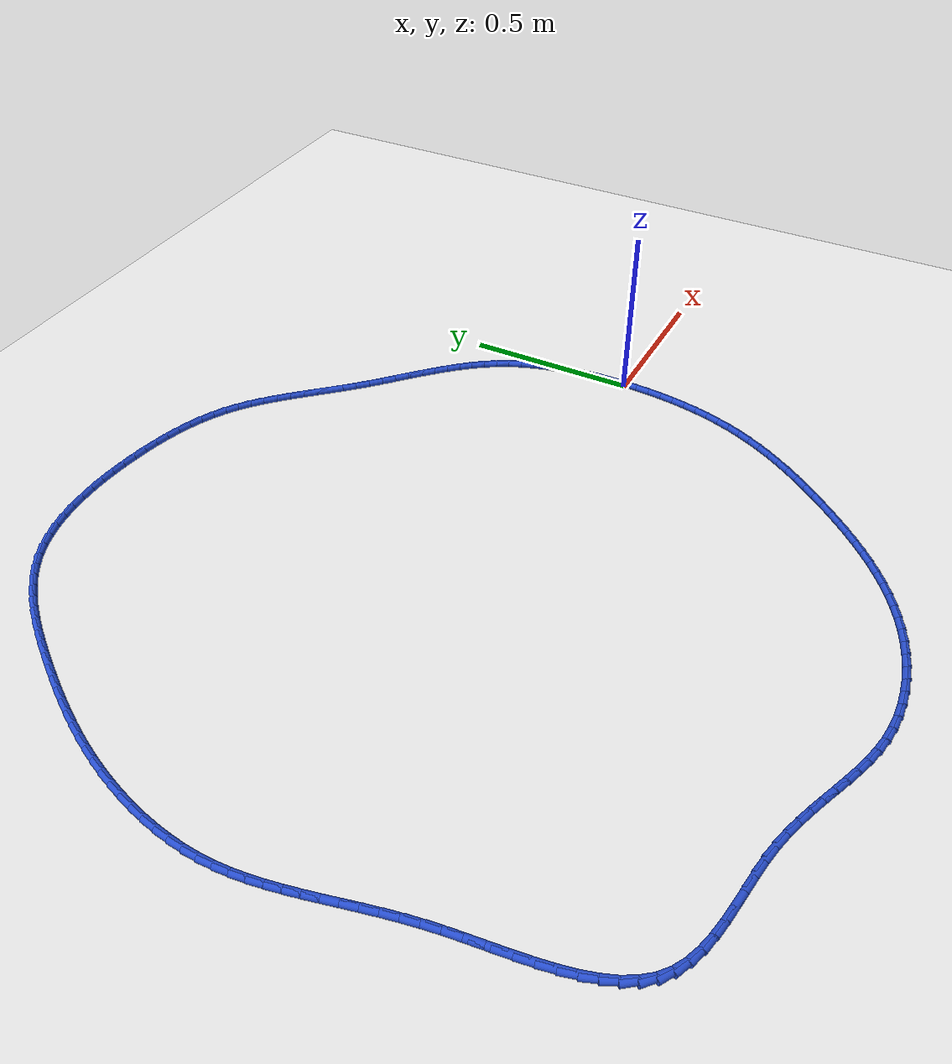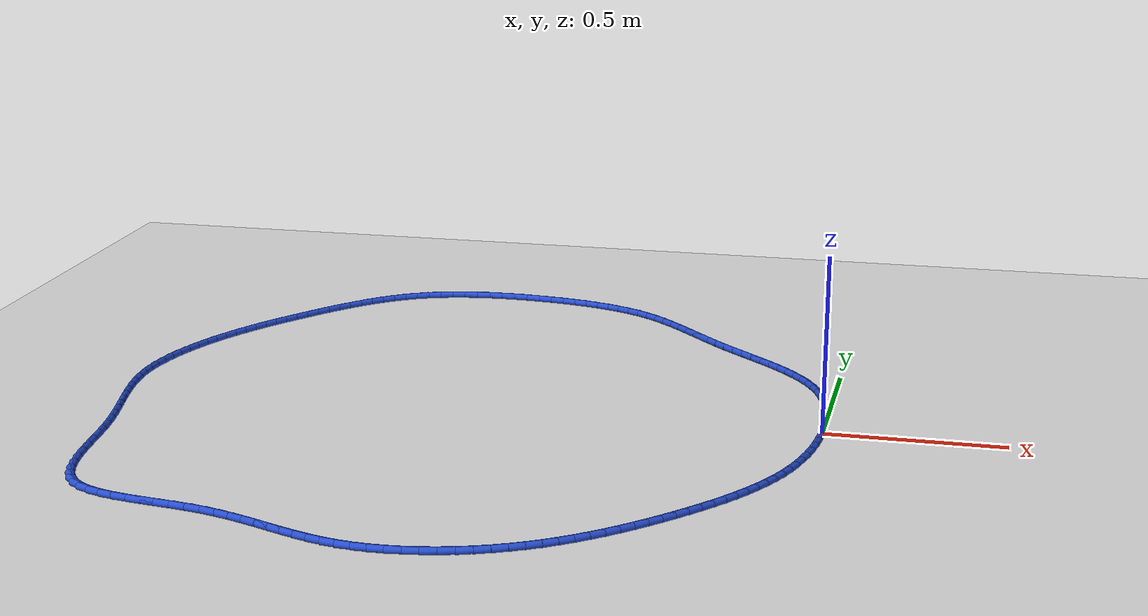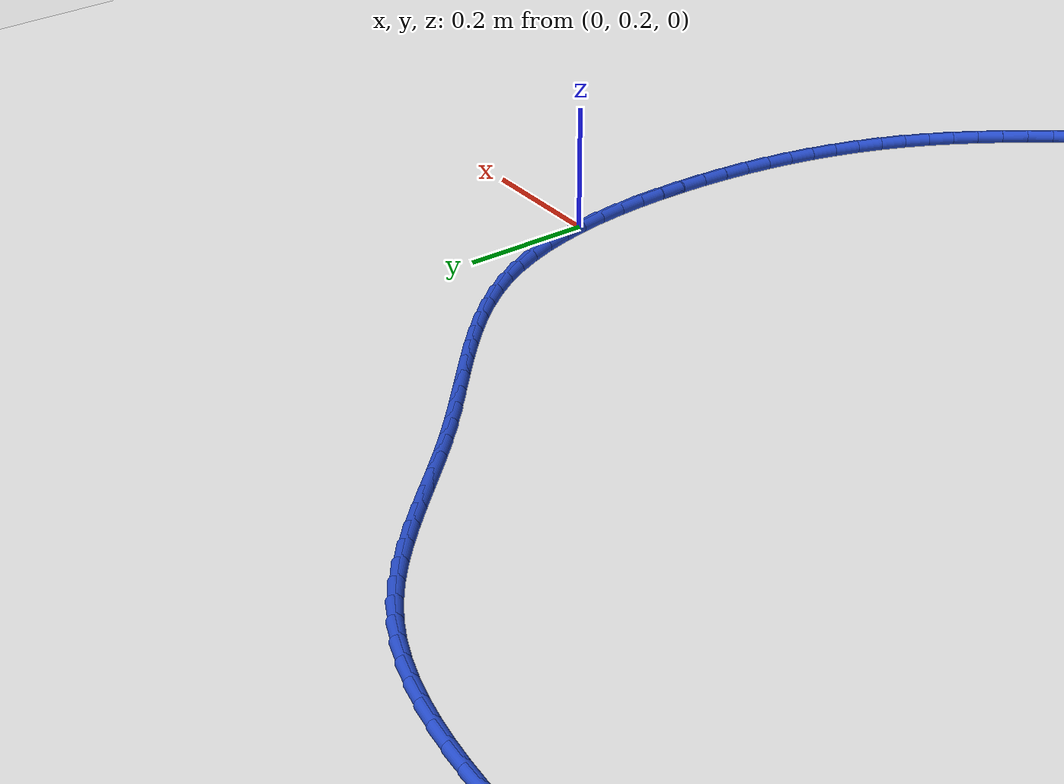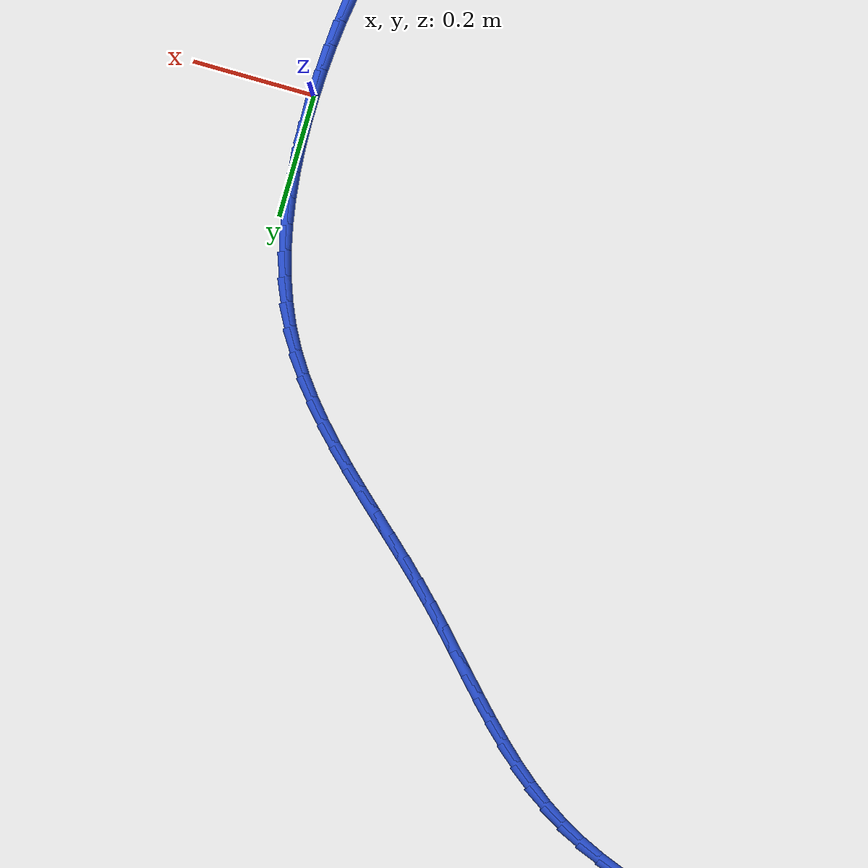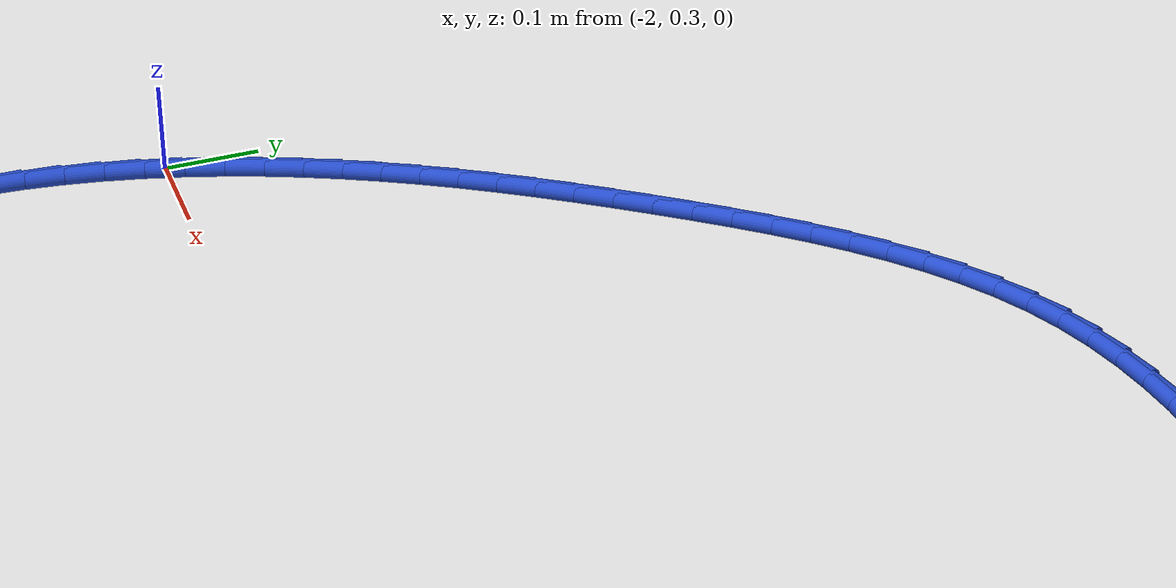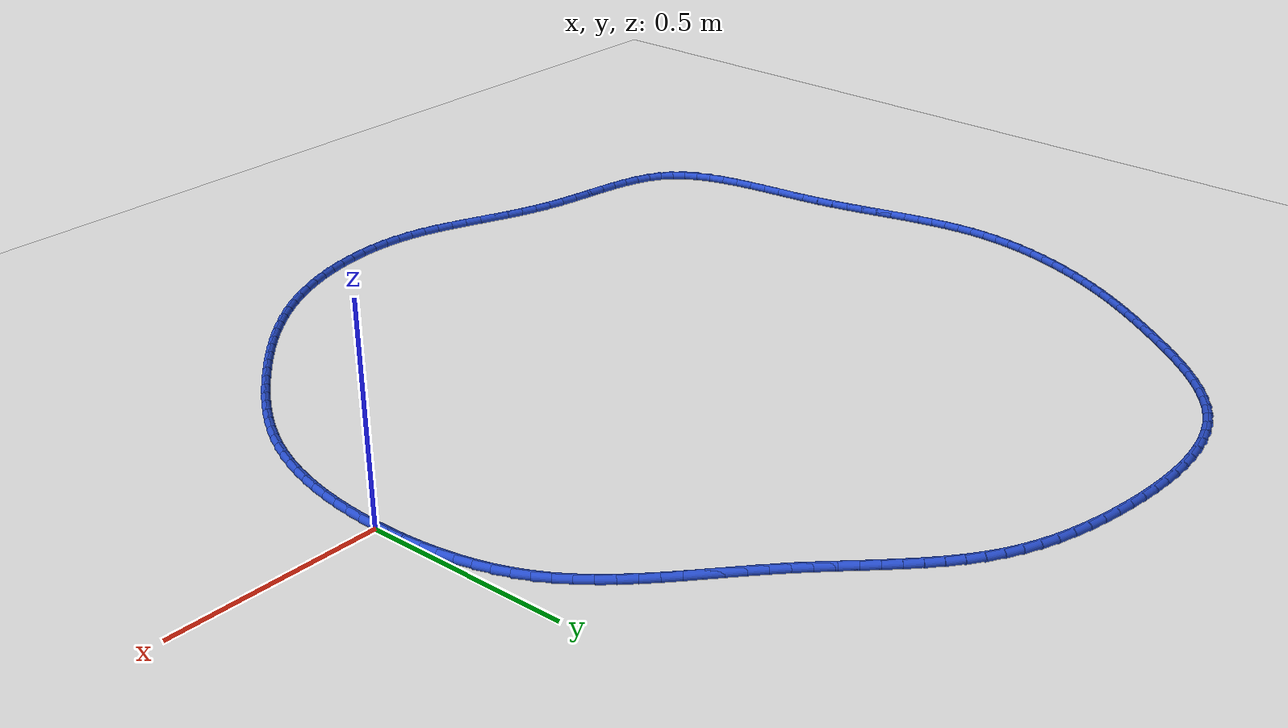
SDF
<sdf version="1.6">
 <world name="default">
  <light name="sun" type="directional">
   <pose>0 0 10 0 -0 0</pose>
   <diffuse>0.8 0.8 0.8 1</diffuse>
   <specular>0.2 0.2 0.2 1</specular>
   <attenuation>
    <range>1000</range>
    <constant>0.9</constant>
    <linear>0.01</linear>
    <quadratic>0.001</quadratic>
   </attenuation>
   <direction>-0.5 0.1 -0.9</direction>
  </light>
  <model name="ground_plane">
   <static>1</static>
   <link name="link">
    <collision name="collision">
     <geometry><plane><normal>0 0 1</normal><size>100 100</size></plane></geometry>
     <surface><friction><ode><mu>100</mu><mu2>50</mu2></ode></friction></surface>
    </collision>
    <visual name="visual">
     <cast_shadows>0</cast_shadows>
     <geometry><plane><normal>0 0 1</normal><size>100 100</size></plane></geometry>
     <material>
      <script><uri>file://media/materials/scripts/gazebo.material</uri><name>Gazebo/WhiteGlow</name></script>
     </material>
    </visual>
   </link>
  </model>
  <gravity>0 0 -9.8</gravity>
  <magnetic_field>6e-06 2.3e-05 -4.2e-05</magnetic_field>
  <atmosphere type="adiabatic"/>
  <physics name="default_physics" default="0" type="ode">
   <max_step_size>0.001</max_step_size>
   <real_time_factor>1</real_time_factor>
   <real_time_update_rate>1000</real_time_update_rate>
  </physics>
  <scene><ambient>0.4 0.4 0.4 1</ambient><background>0.7 0.7 0.7 1</background><shadows>1</shadows></scene>
  <spherical_coordinates>
   <surface_model>EARTH_WGS84</surface_model>
   <latitude_deg>0</latitude_deg>
   <longitude_deg>0</longitude_deg>
   <elevation>0</elevation>
   <heading_deg>0</heading_deg>
  </spherical_coordinates>
  <model name="line">
   <link name="link_0">
    <pose>2.7755575615628914e-17 6.938893903907228e-17 0.01 0 1.57 1.5689100685673707</pose>
    <collision name="collision">
     <geometry><cylinder><radius>0.01</radius><length>0.08</length></cylinder></geometry>
    </collision>
    <visual name="visual">
     <material>
      <script><name>Gazebo/Blue</name><uri>file://media/materials/scripts/gazebo.material</uri></script>
     </material>
     <geometry><cylinder><radius>0.01</radius><length>0.08</length></cylinder></geometry>
    </visual>
   </link>
   <link name="link_1">
    <pose>7.994607583801138e-05 0.042383370344566206 0.01 0 1.57 -1.5371404964698139</pose>
    <collision name="collision">
     <geometry><cylinder><radius>0.01</radius><length>0.08</length></cylinder></geometry>
    </collision>
    <visual name="visual">
     <material>
      <script><name>Gazebo/Blue</name><uri>file://media/materials/scripts/gazebo.material</uri></script>
     </material>
     <geometry><cylinder><radius>0.01</radius><length>0.08</length></cylinder></geometry>
    </visual>
   </link>
   <link name="link_2">
    <pose>-0.0013482450795866082 0.0848025249586542 0.01 0 1.57 -1.4976890243337277</pose>
    <collision name="collision">
     <geometry><cylinder><radius>0.01</radius><length>0.08</length></cylinder></geometry>
    </collision>
    <visual name="visual">
     <material>
      <script><name>Gazebo/Blue</name><uri>file://media/materials/scripts/gazebo.material</uri></script>
     </material>
     <geometry><cylinder><radius>0.01</radius><length>0.08</length></cylinder></geometry>
    </visual>
   </link>
   <link name="link_3">
    <pose>-0.004441875248247093 0.12704340397521033 0.01 0 1.57 -1.4538522677081198</pose>
    <collision name="collision">
     <geometry><cylinder><radius>0.01</radius><length>0.08</length></cylinder></geometry>
    </collision>
    <visual name="visual">
     <material>
      <script><name>Gazebo/Blue</name><uri>file://media/materials/scripts/gazebo.material</uri></script>
     </material>
     <geometry><cylinder><radius>0.01</radius><length>0.08</length></cylinder></geometry>
    </visual>
   </link>
   <link name="link_4">
    <pose>-0.009358246212116686 0.16889194752718073 0.01 0 1.57 -1.4051116423561114</pose>
    <collision name="collision">
     <geometry><cylinder><radius>0.01</radius><length>0.08</length></cylinder></geometry>
    </collision>
    <visual name="visual">
     <material>
      <script><name>Gazebo/Blue</name><uri>file://media/materials/scripts/gazebo.material</uri></script>
     </material>
     <geometry><cylinder><radius>0.01</radius><length>0.08</length></cylinder></geometry>
    </visual>
   </link>
   <link name="link_5">
    <pose>-0.016254659753168657 0.21013409574751185 0.01 0 1.57 -1.350921620914655</pose>
    <collision name="collision">
     <geometry><cylinder><radius>0.01</radius><length>0.08</length></cylinder></geometry>
    </collision>
    <visual name="visual">
     <material>
      <script><name>Gazebo/Blue</name><uri>file://media/materials/scripts/gazebo.material</uri></script>
     </material>
     <geometry><cylinder><radius>0.01</radius><length>0.08</length></cylinder></geometry>
    </visual>
   </link>
   <link name="link_6">
    <pose>-0.02528841765337627 0.2505557887691498 0.01 0 1.57 -1.2907388603148904</pose>
    <collision name="collision">
     <geometry><cylinder><radius>0.01</radius><length>0.08</length></cylinder></geometry>
    </collision>
    <visual name="visual">
     <material>
      <script><name>Gazebo/Blue</name><uri>file://media/materials/scripts/gazebo.material</uri></script>
     </material>
     <geometry><cylinder><radius>0.01</radius><length>0.08</length></cylinder></geometry>
    </visual>
   </link>
   <link name="link_7">
    <pose>-0.03661682169471276 0.289942966725041 0.01 0 1.57 -1.2240700871968735</pose>
    <collision name="collision">
     <geometry><cylinder><radius>0.01</radius><length>0.08</length></cylinder></geometry>
    </collision>
    <visual name="visual">
     <material>
      <script><name>Gazebo/Blue</name><uri>file://media/materials/scripts/gazebo.material</uri></script>
     </material>
     <geometry><cylinder><radius>0.01</radius><length>0.08</length></cylinder></geometry>
    </visual>
   </link>
   <link name="link_8">
    <pose>-0.050397173659151404 0.3280815697481316 0.01 0 1.57 -1.150543545263765</pose>
    <collision name="collision">
     <geometry><cylinder><radius>0.01</radius><length>0.08</length></cylinder></geometry>
    </collision>
    <visual name="visual">
     <material>
      <script><name>Gazebo/Blue</name><uri>file://media/materials/scripts/gazebo.material</uri></script>
     </material>
     <geometry><cylinder><radius>0.01</radius><length>0.08</length></cylinder></geometry>
    </visual>
   </link>
   <link name="link_9">
    <pose>-0.06678677532866543 0.3647575379713679 0.01 0 1.57 -1.0703292855983892</pose>
    <collision name="collision">
     <geometry><cylinder><radius>0.01</radius><length>0.08</length></cylinder></geometry>
    </collision>
    <visual name="visual">
     <material>
      <script><name>Gazebo/Blue</name><uri>file://media/materials/scripts/gazebo.material</uri></script>
     </material>
     <geometry><cylinder><radius>0.01</radius><length>0.08</length></cylinder></geometry>
    </visual>
   </link>
   <link name="link_10">
    <pose>-0.08593309527881403 0.39976577043389694 0.01 0 1.57 -0.9914253341035991</pose>
    <collision name="collision">
     <geometry><cylinder><radius>0.01</radius><length>0.08</length></cylinder></geometry>
    </collision>
    <visual name="visual">
     <material>
      <script><name>Gazebo/Blue</name><uri>file://media/materials/scripts/gazebo.material</uri></script>
     </material>
     <geometry><cylinder><radius>0.01</radius><length>0.08</length></cylinder></geometry>
    </visual>
   </link>
   <link name="link_11">
    <pose>-0.10775114898136404 0.433112951168003 0.01 0 1.57 -0.9225399749263474</pose>
    <collision name="collision">
     <geometry><cylinder><radius>0.01</radius><length>0.08</length></cylinder></geometry>
    </collision>
    <visual name="visual">
     <material>
      <script><name>Gazebo/Blue</name><uri>file://media/materials/scripts/gazebo.material</uri></script>
     </material>
     <geometry><cylinder><radius>0.01</radius><length>0.08</length></cylinder></geometry>
    </visual>
   </link>
   <link name="link_12">
    <pose>-0.1319199500811498 0.46502078239450856 0.01 0 1.57 -0.8645424695875745</pose>
    <collision name="collision">
     <geometry><cylinder><radius>0.01</radius><length>0.08</length></cylinder></geometry>
    </collision>
    <visual name="visual">
     <material>
      <script><name>Gazebo/Blue</name><uri>file://media/materials/scripts/gazebo.material</uri></script>
     </material>
     <geometry><cylinder><radius>0.01</radius><length>0.08</length></cylinder></geometry>
    </visual>
   </link>
   <link name="link_13">
    <pose>-0.15810796922088907 0.4957205719260494 0.01 0 1.57 -0.8174598723026759</pose>
    <collision name="collision">
     <geometry><cylinder><radius>0.01</radius><length>0.08</length></cylinder></geometry>
    </collision>
    <visual name="visual">
     <material>
      <script><name>Gazebo/Blue</name><uri>file://media/materials/scripts/gazebo.material</uri></script>
     </material>
     <geometry><cylinder><radius>0.01</radius><length>0.08</length></cylinder></geometry>
    </visual>
   </link>
   <link name="link_14">
    <pose>-0.18598367704329974 0.5254436275752616 0.01 0 1.57 -0.7810305607558886</pose>
    <collision name="collision">
     <geometry><cylinder><radius>0.01</radius><length>0.08</length></cylinder></geometry>
    </collision>
    <visual name="visual">
     <material>
      <script><name>Gazebo/Blue</name><uri>file://media/materials/scripts/gazebo.material</uri></script>
     </material>
     <geometry><cylinder><radius>0.01</radius><length>0.08</length></cylinder></geometry>
    </visual>
   </link>
   <link name="link_15">
    <pose>-0.2152155441910995 0.5544212571547813 0.01 0 1.57 -0.7548731529399327</pose>
    <collision name="collision">
     <geometry><cylinder><radius>0.01</radius><length>0.08</length></cylinder></geometry>
    </collision>
    <visual name="visual">
     <material>
      <script><name>Gazebo/Blue</name><uri>file://media/materials/scripts/gazebo.material</uri></script>
     </material>
     <geometry><cylinder><radius>0.01</radius><length>0.08</length></cylinder></geometry>
    </visual>
   </link>
   <link name="link_16">
    <pose>-0.24547204130700634 0.5828847684772445 0.01 0 1.57 -0.7386053055957184</pose>
    <collision name="collision">
     <geometry><cylinder><radius>0.01</radius><length>0.08</length></cylinder></geometry>
    </collision>
    <visual name="visual">
     <material>
      <script><name>Gazebo/Blue</name><uri>file://media/materials/scripts/gazebo.material</uri></script>
     </material>
     <geometry><cylinder><radius>0.01</radius><length>0.08</length></cylinder></geometry>
    </visual>
   </link>
   <link name="link_17">
    <pose>-0.2764216390337379 0.611065469355287 0.01 0 1.57 -0.7319170598536419</pose>
    <collision name="collision">
     <geometry><cylinder><radius>0.01</radius><length>0.08</length></cylinder></geometry>
    </collision>
    <visual name="visual">
     <material>
      <script><name>Gazebo/Blue</name><uri>file://media/materials/scripts/gazebo.material</uri></script>
     </material>
     <geometry><cylinder><radius>0.01</radius><length>0.08</length></cylinder></geometry>
    </visual>
   </link>
   <link name="link_18">
    <pose>-0.307732808014012 0.6391946676015449 0.01 0 1.57 -0.7346087441562124</pose>
    <collision name="collision">
     <geometry><cylinder><radius>0.01</radius><length>0.08</length></cylinder></geometry>
    </collision>
    <visual name="visual">
     <material>
      <script><name>Gazebo/Blue</name><uri>file://media/materials/scripts/gazebo.material</uri></script>
     </material>
     <geometry><cylinder><radius>0.01</radius><length>0.08</length></cylinder></geometry>
    </visual>
   </link>
   <link name="link_19">
    <pose>-0.3390740188905465 0.6675036710286545 0.01 0 1.57 -0.7466021573440412</pose>
    <collision name="collision">
     <geometry><cylinder><radius>0.01</radius><length>0.08</length></cylinder></geometry>
    </collision>
    <visual name="visual">
     <material>
      <script><name>Gazebo/Blue</name><uri>file://media/materials/scripts/gazebo.material</uri></script>
     </material>
     <geometry><cylinder><radius>0.01</radius><length>0.08</length></cylinder></geometry>
    </visual>
   </link>
   <link name="link_20">
    <pose>-0.3701137423060592 0.6962237874492514 0.01 0 1.57 -0.7679030759739089</pose>
    <collision name="collision">
     <geometry><cylinder><radius>0.01</radius><length>0.08</length></cylinder></geometry>
    </collision>
    <visual name="visual">
     <material>
      <script><name>Gazebo/Blue</name><uri>file://media/materials/scripts/gazebo.material</uri></script>
     </material>
     <geometry><cylinder><radius>0.01</radius><length>0.08</length></cylinder></geometry>
    </visual>
   </link>
   <link name="link_21">
    <pose>-0.40052126486484535 0.7255855347088467 0.01 0 1.57 -0.7931110564036938</pose>
    <collision name="collision">
     <geometry><cylinder><radius>0.01</radius><length>0.08</length></cylinder></geometry>
    </collision>
    <visual name="visual">
     <material>
      <script><name>Gazebo/Blue</name><uri>file://media/materials/scripts/gazebo.material</uri></script>
     </material>
     <geometry><cylinder><radius>0.01</radius><length>0.08</length></cylinder></geometry>
    </visual>
   </link>
   <link name="link_22">
    <pose>-0.43013300716440966 0.7556576211219381 0.01 0 1.57 -0.8100995542619669</pose>
    <collision name="collision">
     <geometry><cylinder><radius>0.01</radius><length>0.08</length></cylinder></geometry>
    </collision>
    <visual name="visual">
     <material>
      <script><name>Gazebo/Blue</name><uri>file://media/materials/scripts/gazebo.material</uri></script>
     </material>
     <geometry><cylinder><radius>0.01</radius><length>0.08</length></cylinder></geometry>
    </visual>
   </link>
   <link name="link_23">
    <pose>-0.45915545513932926 0.7861504790025189 0.01 0 1.57 -0.8172227649794207</pose>
    <collision name="collision">
     <geometry><cylinder><radius>0.01</radius><length>0.08</length></cylinder></geometry>
    </collision>
    <visual name="visual">
     <material>
      <script><name>Gazebo/Blue</name><uri>file://media/materials/scripts/gazebo.material</uri></script>
     </material>
     <geometry><cylinder><radius>0.01</radius><length>0.08</length></cylinder></geometry>
    </visual>
   </link>
   <link name="link_24">
    <pose>-0.48784473089824404 0.8167264857722645 0.01 0 1.57 -0.8143939105486303</pose>
    <collision name="collision">
     <geometry><cylinder><radius>0.01</radius><length>0.08</length></cylinder></geometry>
    </collision>
    <visual name="visual">
     <material>
      <script><name>Gazebo/Blue</name><uri>file://media/materials/scripts/gazebo.material</uri></script>
     </material>
     <geometry><cylinder><radius>0.01</radius><length>0.08</length></cylinder></geometry>
    </visual>
   </link>
   <link name="link_25">
    <pose>-0.5164569565497934 0.8470480188528491 0.01 0 1.57 -0.8014276752845729</pose>
    <collision name="collision">
     <geometry><cylinder><radius>0.01</radius><length>0.08</length></cylinder></geometry>
    </collision>
    <visual name="visual">
     <material>
      <script><name>Gazebo/Blue</name><uri>file://media/materials/scripts/gazebo.material</uri></script>
     </material>
     <geometry><cylinder><radius>0.01</radius><length>0.08</length></cylinder></geometry>
    </visual>
   </link>
   <link name="link_26">
    <pose>-0.5452482542026176 0.8767774556659486 0.01 0 1.57 -0.7780434507181213</pose>
    <collision name="collision">
     <geometry><cylinder><radius>0.01</radius><length>0.08</length></cylinder></geometry>
    </collision>
    <visual name="visual">
     <material>
      <script><name>Gazebo/Blue</name><uri>file://media/materials/scripts/gazebo.material</uri></script>
     </material>
     <geometry><cylinder><radius>0.01</radius><length>0.08</length></cylinder></geometry>
    </visual>
   </link>
   <link name="link_27">
    <pose>-0.5744747459653562 0.9055771736332373 0.01 0 1.57 -0.7439002639069995</pose>
    <collision name="collision">
     <geometry><cylinder><radius>0.01</radius><length>0.08</length></cylinder></geometry>
    </collision>
    <visual name="visual">
     <material>
      <script><name>Gazebo/Blue</name><uri>file://media/materials/scripts/gazebo.material</uri></script>
     </material>
     <geometry><cylinder><radius>0.01</radius><length>0.08</length></cylinder></geometry>
    </visual>
   </link>
   <link name="link_28">
    <pose>-0.6043925539466491 0.9331095501763912 0.01 0 1.57 -0.6986713291365025</pose>
    <collision name="collision">
     <geometry><cylinder><radius>0.01</radius><length>0.08</length></cylinder></geometry>
    </collision>
    <visual name="visual">
     <material>
      <script><name>Gazebo/Blue</name><uri>file://media/materials/scripts/gazebo.material</uri></script>
     </material>
     <geometry><cylinder><radius>0.01</radius><length>0.08</length></cylinder></geometry>
    </visual>
   </link>
   <link name="link_29">
    <pose>-0.6352578002551361 0.9590369627170845 0.01 0 1.57 -0.6421670598065952</pose>
    <collision name="collision">
     <geometry><cylinder><radius>0.01</radius><length>0.08</length></cylinder></geometry>
    </collision>
    <visual name="visual">
     <material>
      <script><name>Gazebo/Blue</name><uri>file://media/materials/scripts/gazebo.material</uri></script>
     </material>
     <geometry><cylinder><radius>0.01</radius><length>0.08</length></cylinder></geometry>
    </visual>
   </link>
   <link name="link_30">
    <pose>-0.6673266069994568 0.9830217886769923 0.01 0 1.57 -0.5745119205285073</pose>
    <collision name="collision">
     <geometry><cylinder><radius>0.01</radius><length>0.08</length></cylinder></geometry>
    </collision>
    <visual name="visual">
     <material>
      <script><name>Gazebo/Blue</name><uri>file://media/materials/scripts/gazebo.material</uri></script>
     </material>
     <geometry><cylinder><radius>0.01</radius><length>0.08</length></cylinder></geometry>
    </visual>
   </link>
   <link name="link_31">
    <pose>-0.7008550201191719 1.0047264960591102 0.01 0 1.57 -0.4999084351422278</pose>
    <collision name="collision">
     <geometry><cylinder><radius>0.01</radius><length>0.08</length></cylinder></geometry>
    </collision>
    <visual name="visual">
     <material>
      <script><name>Gazebo/Blue</name><uri>file://media/materials/scripts/gazebo.material</uri></script>
     </material>
     <geometry><cylinder><radius>0.01</radius><length>0.08</length></cylinder></geometry>
    </visual>
   </link>
   <link name="link_32">
    <pose>-0.7360053468735837 1.0239250281981043 0.01 0 1.57 -0.4296072061062179</pose>
    <collision name="collision">
     <geometry><cylinder><radius>0.01</radius><length>0.08</length></cylinder></geometry>
    </collision>
    <visual name="visual">
     <material>
      <script><name>Gazebo/Blue</name><uri>file://media/materials/scripts/gazebo.material</uri></script>
     </material>
     <geometry><cylinder><radius>0.01</radius><length>0.08</length></cylinder></geometry>
    </visual>
   </link>
   <link name="link_33">
    <pose>-0.7726636318915434 1.0407198637597672 0.01 0 1.57 -0.3657477749166057</pose>
    <collision name="collision">
     <geometry><cylinder><radius>0.01</radius><length>0.08</length></cylinder></geometry>
    </collision>
    <visual name="visual">
     <material>
      <script><name>Gazebo/Blue</name><uri>file://media/materials/scripts/gazebo.material</uri></script>
     </material>
     <geometry><cylinder><radius>0.01</radius><length>0.08</length></cylinder></geometry>
    </visual>
   </link>
   <link name="link_34">
    <pose>-0.8106652773804605 1.0552737060760748 0.01 0 1.57 -0.3082627211297666</pose>
    <collision name="collision">
     <geometry><cylinder><radius>0.01</radius><length>0.08</length></cylinder></geometry>
    </collision>
    <visual name="visual">
     <material>
      <script><name>Gazebo/Blue</name><uri>file://media/materials/scripts/gazebo.material</uri></script>
     </material>
     <geometry><cylinder><radius>0.01</radius><length>0.08</length></cylinder></geometry>
    </visual>
   </link>
   <link name="link_35">
    <pose>-0.8498456855477432 1.067749258479003 0.01 0 1.57 -0.2569152446970539</pose>
    <collision name="collision">
     <geometry><cylinder><radius>0.01</radius><length>0.08</length></cylinder></geometry>
    </collision>
    <visual name="visual">
     <material>
      <script><name>Gazebo/Blue</name><uri>file://media/materials/scripts/gazebo.material</uri></script>
     </material>
     <geometry><cylinder><radius>0.01</radius><length>0.08</length></cylinder></geometry>
    </visual>
   </link>
   <link name="link_36">
    <pose>-0.8900402586008005 1.0783092243005266 0.01 0 1.57 -0.21137074535099873</pose>
    <collision name="collision">
     <geometry><cylinder><radius>0.01</radius><length>0.08</length></cylinder></geometry>
    </collision>
    <visual name="visual">
     <material>
      <script><name>Gazebo/Blue</name><uri>file://media/materials/scripts/gazebo.material</uri></script>
     </material>
     <geometry><cylinder><radius>0.01</radius><length>0.08</length></cylinder></geometry>
    </visual>
   </link>
   <link name="link_37">
    <pose>-0.9310843987470419 1.0871163068726226 0.01 0 1.57 -0.17125247584225567</pose>
    <collision name="collision">
     <geometry><cylinder><radius>0.01</radius><length>0.08</length></cylinder></geometry>
    </collision>
    <visual name="visual">
     <material>
      <script><name>Gazebo/Blue</name><uri>file://media/materials/scripts/gazebo.material</uri></script>
     </material>
     <geometry><cylinder><radius>0.01</radius><length>0.08</length></cylinder></geometry>
    </visual>
   </link>
   <link name="link_38">
    <pose>-0.9728135081938752 1.0943332095272662 0.01 0 1.57 -0.13618138255534126</pose>
    <collision name="collision">
     <geometry><cylinder><radius>0.01</radius><length>0.08</length></cylinder></geometry>
    </collision>
    <visual name="visual">
     <material>
      <script><name>Gazebo/Blue</name><uri>file://media/materials/scripts/gazebo.material</uri></script>
     </material>
     <geometry><cylinder><radius>0.01</radius><length>0.08</length></cylinder></geometry>
    </visual>
   </link>
   <link name="link_39">
    <pose>-1.0150629891487095 1.1001226355964326 0.01 0 1.57 -0.10517898835809106</pose>
    <collision name="collision">
     <geometry><cylinder><radius>0.01</radius><length>0.08</length></cylinder></geometry>
    </collision>
    <visual name="visual">
     <material>
      <script><name>Gazebo/Blue</name><uri>file://media/materials/scripts/gazebo.material</uri></script>
     </material>
     <geometry><cylinder><radius>0.01</radius><length>0.08</length></cylinder></geometry>
    </visual>
   </link>
   <link name="link_40">
    <pose>-1.0576666466667994 1.1046202425440002 0.01 0 1.57 -0.07295500872507307</pose>
    <collision name="collision">
     <geometry><cylinder><radius>0.01</radius><length>0.08</length></cylinder></geometry>
    </collision>
    <visual name="visual">
     <material>
      <script><name>Gazebo/Blue</name><uri>file://media/materials/scripts/gazebo.material</uri></script>
     </material>
     <geometry><cylinder><radius>0.01</radius><length>0.08</length></cylinder></geometry>
    </visual>
   </link>
   <link name="link_41">
    <pose>-1.1004455917793654 1.1077467296668368 0.01 0 1.57 -0.03677361657779231</pose>
    <collision name="collision">
     <geometry><cylinder><radius>0.01</radius><length>0.08</length></cylinder></geometry>
    </collision>
    <visual name="visual">
     <material>
      <script><name>Gazebo/Blue</name><uri>file://media/materials/scripts/gazebo.material</uri></script>
     </material>
     <geometry><cylinder><radius>0.01</radius><length>0.08</length></cylinder></geometry>
    </visual>
   </link>
   <link name="link_42">
    <pose>-1.1432148780544125 1.1093202203421304 0.01 0 1.57 0.0038054353172262538</pose>
    <collision name="collision">
     <geometry><cylinder><radius>0.01</radius><length>0.08</length></cylinder></geometry>
    </collision>
    <visual name="visual">
     <material>
      <script><name>Gazebo/Blue</name><uri>file://media/materials/scripts/gazebo.material</uri></script>
     </material>
     <geometry><cylinder><radius>0.01</radius><length>0.08</length></cylinder></geometry>
    </visual>
   </link>
   <link name="link_43">
    <pose>-1.185789521653157 1.109158204507692 0.01 0 1.57 0.049255815760416696</pose>
    <collision name="collision">
     <geometry><cylinder><radius>0.01</radius><length>0.08</length></cylinder></geometry>
    </collision>
    <visual name="visual">
     <material>
      <script><name>Gazebo/Blue</name><uri>file://media/materials/scripts/gazebo.material</uri></script>
     </material>
     <geometry><cylinder><radius>0.01</radius><length>0.08</length></cylinder></geometry>
    </visual>
   </link>
   <link name="link_44">
    <pose>-1.227984538736816 1.1070781721013325 0.01 0 1.57 0.10008527572492634</pose>
    <collision name="collision">
     <geometry><cylinder><radius>0.01</radius><length>0.08</length></cylinder></geometry>
    </collision>
    <visual name="visual">
     <material>
      <script><name>Gazebo/Blue</name><uri>file://media/materials/scripts/gazebo.material</uri></script>
     </material>
     <geometry><cylinder><radius>0.01</radius><length>0.08</length></cylinder></geometry>
    </visual>
   </link>
   <link name="link_45">
    <pose>-1.2696149454666046 1.1028976130608628 0.01 0 1.57 0.15681023764077648</pose>
    <collision name="collision">
     <geometry><cylinder><radius>0.01</radius><length>0.08</length></cylinder></geometry>
    </collision>
    <visual name="visual">
     <material>
      <script><name>Gazebo/Blue</name><uri>file://media/materials/scripts/gazebo.material</uri></script>
     </material>
     <geometry><cylinder><radius>0.01</radius><length>0.08</length></cylinder></geometry>
    </visual>
   </link>
   <link name="link_46">
    <pose>-1.3104957580037417 1.0964340173240945 0.01 0 1.57 0.21991389838990455</pose>
    <collision name="collision">
     <geometry><cylinder><radius>0.01</radius><length>0.08</length></cylinder></geometry>
    </collision>
    <visual name="visual">
     <material>
      <script><name>Gazebo/Blue</name><uri>file://media/materials/scripts/gazebo.material</uri></script>
     </material>
     <geometry><cylinder><radius>0.01</radius><length>0.08</length></cylinder></geometry>
    </visual>
   </link>
   <link name="link_47">
    <pose>-1.3504419925094417 1.0875048748288376 0.01 0 1.57 0.28978297204122794</pose>
    <collision name="collision">
     <geometry><cylinder><radius>0.01</radius><length>0.08</length></cylinder></geometry>
    </collision>
    <visual name="visual">
     <material>
      <script><name>Gazebo/Blue</name><uri>file://media/materials/scripts/gazebo.material</uri></script>
     </material>
     <geometry><cylinder><radius>0.01</radius><length>0.08</length></cylinder></geometry>
    </visual>
   </link>
   <link name="link_48">
    <pose>-1.3892686651449218 1.0759276755129035 0.01 0 1.57 0.3666206731034478</pose>
    <collision name="collision">
     <geometry><cylinder><radius>0.01</radius><length>0.08</length></cylinder></geometry>
    </collision>
    <visual name="visual">
     <material>
      <script><name>Gazebo/Blue</name><uri>file://media/materials/scripts/gazebo.material</uri></script>
     </material>
     <geometry><cylinder><radius>0.01</radius><length>0.08</length></cylinder></geometry>
    </visual>
   </link>
   <link name="link_49">
    <pose>-1.4267907920713987 1.0615199093141034 0.01 0 1.57 0.4503375389906583</pose>
    <collision name="collision">
     <geometry><cylinder><radius>0.01</radius><length>0.08</length></cylinder></geometry>
    </collision>
    <visual name="visual">
     <material>
      <script><name>Gazebo/Blue</name><uri>file://media/materials/scripts/gazebo.material</uri></script>
     </material>
     <geometry><cylinder><radius>0.01</radius><length>0.08</length></cylinder></geometry>
    </visual>
   </link>
   <link name="link_50">
    <pose>-1.4628234399773667 1.0440991533385167 0.01 0 1.57 0.5371897602432852</pose>
    <collision name="collision">
     <geometry><cylinder><radius>0.01</radius><length>0.08</length></cylinder></geometry>
    </collision>
    <visual name="visual">
     <material>
      <script><name>Gazebo/Blue</name><uri>file://media/materials/scripts/gazebo.material</uri></script>
     </material>
     <geometry><cylinder><radius>0.01</radius><length>0.08</length></cylinder></geometry>
    </visual>
   </link>
   <link name="link_51">
    <pose>-1.4972471070402358 1.023595865294979 0.01 0 1.57 0.6167905847550336</pose>
    <collision name="collision">
     <geometry><cylinder><radius>0.01</radius><length>0.08</length></cylinder></geometry>
    </collision>
    <visual name="visual">
     <material>
      <script><name>Gazebo/Blue</name><uri>file://media/materials/scripts/gazebo.material</uri></script>
     </material>
     <geometry><cylinder><radius>0.01</radius><length>0.08</length></cylinder></geometry>
    </visual>
   </link>
   <link name="link_52">
    <pose>-1.530136202344044 1.000275032648325 0.01 0 1.57 0.6870203333192387</pose>
    <collision name="collision">
     <geometry><cylinder><radius>0.01</radius><length>0.08</length></cylinder></geometry>
    </collision>
    <visual name="visual">
     <material>
      <script><name>Gazebo/Blue</name><uri>file://media/materials/scripts/gazebo.material</uri></script>
     </material>
     <geometry><cylinder><radius>0.01</radius><length>0.08</length></cylinder></geometry>
    </visual>
   </link>
   <link name="link_53">
    <pose>-1.5616008880451686 0.9744633230791814 0.01 0 1.57 0.7480053871471516</pose>
    <collision name="collision">
     <geometry><cylinder><radius>0.01</radius><length>0.08</length></cylinder></geometry>
    </collision>
    <visual name="visual">
     <material>
      <script><name>Gazebo/Blue</name><uri>file://media/materials/scripts/gazebo.material</uri></script>
     </material>
     <geometry><cylinder><radius>0.01</radius><length>0.08</length></cylinder></geometry>
    </visual>
   </link>
   <link name="link_54">
    <pose>-1.591751326299986 0.9464874042681749 0.01 0 1.57 0.8001539024800867</pose>
    <collision name="collision">
     <geometry><cylinder><radius>0.01</radius><length>0.08</length></cylinder></geometry>
    </collision>
    <visual name="visual">
     <material>
      <script><name>Gazebo/Blue</name><uri>file://media/materials/scripts/gazebo.material</uri></script>
     </material>
     <geometry><cylinder><radius>0.01</radius><length>0.08</length></cylinder></geometry>
    </visual>
   </link>
   <link name="link_55">
    <pose>-1.6206976792648724 0.9166739438959319 0.01 0 1.57 0.8440010465876947</pose>
    <collision name="collision">
     <geometry><cylinder><radius>0.01</radius><length>0.08</length></cylinder></geometry>
    </collision>
    <visual name="visual">
     <material>
      <script><name>Gazebo/Blue</name><uri>file://media/materials/scripts/gazebo.material</uri></script>
     </material>
     <geometry><cylinder><radius>0.01</radius><length>0.08</length></cylinder></geometry>
    </visual>
   </link>
   <link name="link_56">
    <pose>-1.648550109096205 0.8853496096430784 0.01 0 1.57 0.880097831313926</pose>
    <collision name="collision">
     <geometry><cylinder><radius>0.01</radius><length>0.08</length></cylinder></geometry>
    </collision>
    <visual name="visual">
     <material>
      <script><name>Gazebo/Blue</name><uri>file://media/materials/scripts/gazebo.material</uri></script>
     </material>
     <geometry><cylinder><radius>0.01</radius><length>0.08</length></cylinder></geometry>
    </visual>
   </link>
   <link name="link_57">
    <pose>-1.675418777950359 0.8528410691902413 0.01 0 1.57 0.9089380846560258</pose>
    <collision name="collision">
     <geometry><cylinder><radius>0.01</radius><length>0.08</length></cylinder></geometry>
    </collision>
    <visual name="visual">
     <material>
      <script><name>Gazebo/Blue</name><uri>file://media/materials/scripts/gazebo.material</uri></script>
     </material>
     <geometry><cylinder><radius>0.01</radius><length>0.08</length></cylinder></geometry>
    </visual>
   </link>
   <link name="link_58">
    <pose>-1.7014138479837129 0.8194749902180467 0.01 0 1.57 0.9309127059710687</pose>
    <collision name="collision">
     <geometry><cylinder><radius>0.01</radius><length>0.08</length></cylinder></geometry>
    </collision>
    <visual name="visual">
     <material>
      <script><name>Gazebo/Blue</name><uri>file://media/materials/scripts/gazebo.material</uri></script>
     </material>
     <geometry><cylinder><radius>0.01</radius><length>0.08</length></cylinder></geometry>
    </visual>
   </link>
   <link name="link_59">
    <pose>-1.7266454813526415 0.785578040407122 0.01 0 1.57 0.9463329965080772</pose>
    <collision name="collision">
     <geometry><cylinder><radius>0.01</radius><length>0.08</length></cylinder></geometry>
    </collision>
    <visual name="visual">
     <material>
      <script><name>Gazebo/Blue</name><uri>file://media/materials/scripts/gazebo.material</uri></script>
     </material>
     <geometry><cylinder><radius>0.01</radius><length>0.08</length></cylinder></geometry>
    </visual>
   </link>
   <link name="link_60">
    <pose>-1.7512228388067657 0.7514744967652388 0.01 0 1.57 0.9586693720810079</pose>
    <collision name="collision">
     <geometry><cylinder><radius>0.01</radius><length>0.08</length></cylinder></geometry>
    </collision>
    <visual name="visual">
     <material>
      <script><name>Gazebo/Blue</name><uri>file://media/materials/scripts/gazebo.material</uri></script>
     </material>
     <geometry><cylinder><radius>0.01</radius><length>0.08</length></cylinder></geometry>
    </visual>
   </link>
   <link name="link_61">
    <pose>-1.7751911353999055 0.7173359778144072 0.01 0 1.57 0.9732770989073142</pose>
    <collision name="collision">
     <geometry><cylinder><radius>0.01</radius><length>0.08</length></cylinder></geometry>
    </collision>
    <visual name="visual">
     <material>
      <script><name>Gazebo/Blue</name><uri>file://media/materials/scripts/gazebo.material</uri></script>
     </material>
     <geometry><cylinder><radius>0.01</radius><length>0.08</length></cylinder></geometry>
    </visual>
   </link>
   <link name="link_62">
    <pose>-1.798494183957913 0.6830920230691159 0.01 0 1.57 0.990638955249911</pose>
    <collision name="collision">
     <geometry><cylinder><radius>0.01</radius><length>0.08</length></cylinder></geometry>
    </collision>
    <visual name="visual">
     <material>
      <script><name>Gazebo/Blue</name><uri>file://media/materials/scripts/gazebo.material</uri></script>
     </material>
     <geometry><cylinder><radius>0.01</radius><length>0.08</length></cylinder></geometry>
    </visual>
   </link>
   <link name="link_63">
    <pose>-1.8210668017229703 0.6486506967566651 0.01 0 1.57 1.010741564695442</pose>
    <collision name="collision">
     <geometry><cylinder><radius>0.01</radius><length>0.08</length></cylinder></geometry>
    </collision>
    <visual name="visual">
     <material>
      <script><name>Gazebo/Blue</name><uri>file://media/materials/scripts/gazebo.material</uri></script>
     </material>
     <geometry><cylinder><radius>0.01</radius><length>0.08</length></cylinder></geometry>
    </visual>
   </link>
   <link name="link_64">
    <pose>-1.842843805937259 0.6139200631043558 0.01 0 1.57 1.0335432675178449</pose>
    <collision name="collision">
     <geometry><cylinder><radius>0.01</radius><length>0.08</length></cylinder></geometry>
    </collision>
    <visual name="visual">
     <material>
      <script><name>Gazebo/Blue</name><uri>file://media/materials/scripts/gazebo.material</uri></script>
     </material>
     <geometry><cylinder><radius>0.01</radius><length>0.08</length></cylinder></geometry>
    </visual>
   </link>
   <link name="link_65">
    <pose>-1.86376001384296 0.578808186339488 0.01 0 1.57 1.0589698647585044</pose>
    <collision name="collision">
     <geometry><cylinder><radius>0.01</radius><length>0.08</length></cylinder></geometry>
    </collision>
    <visual name="visual">
     <material>
      <script><name>Gazebo/Blue</name><uri>file://media/materials/scripts/gazebo.material</uri></script>
     </material>
     <geometry><cylinder><radius>0.01</radius><length>0.08</length></cylinder></geometry>
    </visual>
   </link>
   <link name="link_66">
    <pose>-1.8837502426822552 0.5432231306893622 0.01 0 1.57 1.086910783392453</pose>
    <collision name="collision">
     <geometry><cylinder><radius>0.01</radius><length>0.08</length></cylinder></geometry>
    </collision>
    <visual name="visual">
     <material>
      <script><name>Gazebo/Blue</name><uri>file://media/materials/scripts/gazebo.material</uri></script>
     </material>
     <geometry><cylinder><radius>0.01</radius><length>0.08</length></cylinder></geometry>
    </visual>
   </link>
   <link name="link_67">
    <pose>-1.9027493096973278 0.5070729603812798 0.01 0 1.57 1.1172161411557868</pose>
    <collision name="collision">
     <geometry><cylinder><radius>0.01</radius><length>0.08</length></cylinder></geometry>
    </collision>
    <visual name="visual">
     <material>
      <script><name>Gazebo/Blue</name><uri>file://media/materials/scripts/gazebo.material</uri></script>
     </material>
     <geometry><cylinder><radius>0.01</radius><length>0.08</length></cylinder></geometry>
    </visual>
   </link>
   <link name="link_68">
    <pose>-1.920692032130357 0.4702657396425401 0.01 0 1.57 1.149695234886255</pose>
    <collision name="collision">
     <geometry><cylinder><radius>0.01</radius><length>0.08</length></cylinder></geometry>
    </collision>
    <visual name="visual">
     <material>
      <script><name>Gazebo/Blue</name><uri>file://media/materials/scripts/gazebo.material</uri></script>
     </material>
     <geometry><cylinder><radius>0.01</radius><length>0.08</length></cylinder></geometry>
    </visual>
   </link>
   <link name="link_69">
    <pose>-1.9375132272235256 0.43270953270044465 0.01 0 1.57 1.1841154487596448</pose>
    <collision name="collision">
     <geometry><cylinder><radius>0.01</radius><length>0.08</length></cylinder></geometry>
    </collision>
    <visual name="visual">
     <material>
      <script><name>Gazebo/Blue</name><uri>file://media/materials/scripts/gazebo.material</uri></script>
     </material>
     <geometry><cylinder><radius>0.01</radius><length>0.08</length></cylinder></geometry>
    </visual>
   </link>
   <link name="link_70">
    <pose>-1.9531452850895212 0.39431853015060836 0.01 0 1.57 1.2203140845607783</pose>
    <collision name="collision">
     <geometry><cylinder><radius>0.01</radius><length>0.08</length></cylinder></geometry>
    </collision>
    <visual name="visual">
     <material>
      <script><name>Gazebo/Blue</name><uri>file://media/materials/scripts/gazebo.material</uri></script>
     </material>
     <geometry><cylinder><radius>0.01</radius><length>0.08</length></cylinder></geometry>
    </visual>
   </link>
   <link name="link_71">
    <pose>-1.9674692486547496 0.35513652909536164 0.01 0 1.57 1.258585240429816</pose>
    <collision name="collision">
     <geometry><cylinder><radius>0.01</radius><length>0.08</length></cylinder></geometry>
    </collision>
    <visual name="visual">
     <material>
      <script><name>Gazebo/Blue</name><uri>file://media/materials/scripts/gazebo.material</uri></script>
     </material>
     <geometry><cylinder><radius>0.01</radius><length>0.08</length></cylinder></geometry>
    </visual>
   </link>
   <link name="link_72">
    <pose>-1.9803171840982203 0.3153309498693828 0.01 0 1.57 1.2993981332020452</pose>
    <collision name="collision">
     <geometry><cylinder><radius>0.01</radius><length>0.08</length></cylinder></geometry>
    </collision>
    <visual name="visual">
     <material>
      <script><name>Gazebo/Blue</name><uri>file://media/materials/scripts/gazebo.material</uri></script>
     </material>
     <geometry><cylinder><radius>0.01</radius><length>0.08</length></cylinder></geometry>
    </visual>
   </link>
   <link name="link_73">
    <pose>-1.991519204889255 0.2750741416827151 0.01 0 1.57 1.3432520740090117</pose>
    <collision name="collision">
     <geometry><cylinder><radius>0.01</radius><length>0.08</length></cylinder></geometry>
    </collision>
    <visual name="visual">
     <material>
      <script><name>Gazebo/Blue</name><uri>file://media/materials/scripts/gazebo.material</uri></script>
     </material>
     <geometry><cylinder><radius>0.01</radius><length>0.08</length></cylinder></geometry>
    </visual>
   </link>
   <link name="link_74">
    <pose>-2.0009054244971742 0.23453845374540314 0.01 0 1.57 1.3906799498544182</pose>
    <collision name="collision">
     <geometry><cylinder><radius>0.01</radius><length>0.08</length></cylinder></geometry>
    </collision>
    <visual name="visual">
     <material>
      <script><name>Gazebo/Blue</name><uri>file://media/materials/scripts/gazebo.material</uri></script>
     </material>
     <geometry><cylinder><radius>0.01</radius><length>0.08</length></cylinder></geometry>
    </visual>
   </link>
   <link name="link_75">
    <pose>-2.0083059563912977 0.19389623526749064 0.01 0 1.57 1.442247827732246</pose>
    <collision name="collision">
     <geometry><cylinder><radius>0.01</radius><length>0.08</length></cylinder></geometry>
    </collision>
    <visual name="visual">
     <material>
      <script><name>Gazebo/Blue</name><uri>file://media/materials/scripts/gazebo.material</uri></script>
     </material>
     <geometry><cylinder><radius>0.01</radius><length>0.08</length></cylinder></geometry>
    </visual>
   </link>
   <link name="link_76">
    <pose>-2.0135509140409464 0.1533198354590212 0.01 0 1.57 1.498546873659196</pose>
    <collision name="collision">
     <geometry><cylinder><radius>0.01</radius><length>0.08</length></cylinder></geometry>
    </collision>
    <visual name="visual">
     <material>
      <script><name>Gazebo/Blue</name><uri>file://media/materials/scripts/gazebo.material</uri></script>
     </material>
     <geometry><cylinder><radius>0.01</radius><length>0.08</length></cylinder></geometry>
    </visual>
   </link>
   <link name="link_77">
    <pose>-2.0164704109154417 0.11298160353003958 0.01 0 1.57 1.5600231100559157</pose>
    <collision name="collision">
     <geometry><cylinder><radius>0.01</radius><length>0.08</length></cylinder></geometry>
    </collision>
    <visual name="visual">
     <material>
      <script><name>Gazebo/Blue</name><uri>file://media/materials/scripts/gazebo.material</uri></script>
     </material>
     <geometry><cylinder><radius>0.01</radius><length>0.08</length></cylinder></geometry>
    </visual>
   </link>
   <link name="link_78">
    <pose>-2.016900619123803 0.07305002366688354 0.01 0 1.57 -1.5200040323658288</pose>
    <collision name="collision">
     <geometry><cylinder><radius>0.01</radius><length>0.08</length></cylinder></geometry>
    </collision>
    <visual name="visual">
     <material>
      <script><name>Gazebo/Blue</name><uri>file://media/materials/scripts/gazebo.material</uri></script>
     </material>
     <geometry><cylinder><radius>0.01</radius><length>0.08</length></cylinder></geometry>
    </visual>
   </link>
   <link name="link_79">
    <pose>-2.014892915125048 0.03355629347750475 0.01 0 1.57 -1.4659188262807188</pose>
    <collision name="collision">
     <geometry><cylinder><radius>0.01</radius><length>0.08</length></cylinder></geometry>
    </collision>
    <visual name="visual">
     <material>
      <script><name>Gazebo/Blue</name><uri>file://media/materials/scripts/gazebo.material</uri></script>
     </material>
     <geometry><cylinder><radius>0.01</radius><length>0.08</length></cylinder></geometry>
    </visual>
   </link>
   <link name="link_80">
    <pose>-2.0107670123664168 -0.005639571225354064 0.01 0 1.57 -1.4206485619733698</pose>
    <collision name="collision">
     <geometry><cylinder><radius>0.01</radius><length>0.08</length></cylinder></geometry>
    </collision>
    <visual name="visual">
     <material>
      <script><name>Gazebo/Blue</name><uri>file://media/materials/scripts/gazebo.material</uri></script>
     </material>
     <geometry><cylinder><radius>0.01</radius><length>0.08</length></cylinder></geometry>
    </visual>
   </link>
   <link name="link_81">
    <pose>-2.0048594719169923 -0.04468830233156936 0.01 0 1.57 -1.3846988196718093</pose>
    <collision name="collision">
     <geometry><cylinder><radius>0.01</radius><length>0.08</length></cylinder></geometry>
    </collision>
    <visual name="visual">
     <material>
      <script><name>Gazebo/Blue</name><uri>file://media/materials/scripts/gazebo.material</uri></script>
     </material>
     <geometry><cylinder><radius>0.01</radius><length>0.08</length></cylinder></geometry>
    </visual>
   </link>
   <link name="link_82">
    <pose>-1.997506854845853 -0.08374063173101816 0.01 0 1.57 -1.3582474626516305</pose>
    <collision name="collision">
     <geometry><cylinder><radius>0.01</radius><length>0.08</length></cylinder></geometry>
    </collision>
    <visual name="visual">
     <material>
      <script><name>Gazebo/Blue</name><uri>file://media/materials/scripts/gazebo.material</uri></script>
     </material>
     <geometry><cylinder><radius>0.01</radius><length>0.08</length></cylinder></geometry>
    </visual>
   </link>
   <link name="link_83">
    <pose>-1.989045722222081 -0.12294729131357554 0.01 0 1.57 -1.3412359398261178</pose>
    <collision name="collision">
     <geometry><cylinder><radius>0.01</radius><length>0.08</length></cylinder></geometry>
    </collision>
    <visual name="visual">
     <material>
      <script><name>Gazebo/Blue</name><uri>file://media/materials/scripts/gazebo.material</uri></script>
     </material>
     <geometry><cylinder><radius>0.01</radius><length>0.08</length></cylinder></geometry>
    </visual>
   </link>
   <link name="link_84">
    <pose>-1.9798126351147547 -0.16245901296911858 0.01 0 1.57 -1.333447600823755</pose>
    <collision name="collision">
     <geometry><cylinder><radius>0.01</radius><length>0.08</length></cylinder></geometry>
    </collision>
    <visual name="visual">
     <material>
      <script><name>Gazebo/Blue</name><uri>file://media/materials/scripts/gazebo.material</uri></script>
     </material>
     <geometry><cylinder><radius>0.01</radius><length>0.08</length></cylinder></geometry>
    </visual>
   </link>
   <link name="link_85">
    <pose>-1.9701441545929568 -0.2024265285875237 0.01 0 1.57 -1.3345629921398494</pose>
    <collision name="collision">
     <geometry><cylinder><radius>0.01</radius><length>0.08</length></cylinder></geometry>
    </collision>
    <visual name="visual">
     <material>
      <script><name>Gazebo/Blue</name><uri>file://media/materials/scripts/gazebo.material</uri></script>
     </material>
     <geometry><cylinder><radius>0.01</radius><length>0.08</length></cylinder></geometry>
    </visual>
   </link>
   <link name="link_86">
    <pose>-1.9603768417257665 -0.24300057005866732 0.01 0 1.57 -1.3441906305630849</pose>
    <collision name="collision">
     <geometry><cylinder><radius>0.01</radius><length>0.08</length></cylinder></geometry>
    </collision>
    <visual name="visual">
     <material>
      <script><name>Gazebo/Blue</name><uri>file://media/materials/scripts/gazebo.material</uri></script>
     </material>
     <geometry><cylinder><radius>0.01</radius><length>0.08</length></cylinder></geometry>
    </visual>
   </link>
   <link name="link_87">
    <pose>-1.9508472575822648 -0.2843318692724266 0.01 0 1.57 -1.3618765763833711</pose>
    <collision name="collision">
     <geometry><cylinder><radius>0.01</radius><length>0.08</length></cylinder></geometry>
    </collision>
    <visual name="visual">
     <material>
      <script><name>Gazebo/Blue</name><uri>file://media/materials/scripts/gazebo.material</uri></script>
     </material>
     <geometry><cylinder><radius>0.01</radius><length>0.08</length></cylinder></geometry>
    </visual>
   </link>
   <link name="link_88">
    <pose>-1.9418919632315321 -0.32657115811867643 0.01 0 1.57 -1.387098441997999</pose>
    <collision name="collision">
     <geometry><cylinder><radius>0.01</radius><length>0.08</length></cylinder></geometry>
    </collision>
    <visual name="visual">
     <material>
      <script><name>Gazebo/Blue</name><uri>file://media/materials/scripts/gazebo.material</uri></script>
     </material>
     <geometry><cylinder><radius>0.01</radius><length>0.08</length></cylinder></geometry>
    </visual>
   </link>
   <link name="link_89">
    <pose>-1.9338475197426486 -0.3698691684872939 0.01 0 1.57 -1.41861866611452</pose>
    <collision name="collision">
     <geometry><cylinder><radius>0.01</radius><length>0.08</length></cylinder></geometry>
    </collision>
    <visual name="visual">
     <material>
      <script><name>Gazebo/Blue</name><uri>file://media/materials/scripts/gazebo.material</uri></script>
     </material>
     <geometry><cylinder><radius>0.01</radius><length>0.08</length></cylinder></geometry>
    </visual>
   </link>
   <link name="link_90">
    <pose>-1.927024872825953 -0.4143559809340505 0.01 0 1.57 -1.4447960417823538</pose>
    <collision name="collision">
     <geometry><cylinder><radius>0.01</radius><length>0.08</length></cylinder></geometry>
    </collision>
    <visual name="visual">
     <material>
      <script><name>Gazebo/Blue</name><uri>file://media/materials/scripts/gazebo.material</uri></script>
     </material>
     <geometry><cylinder><radius>0.01</radius><length>0.08</length></cylinder></geometry>
    </visual>
   </link>
   <link name="link_91">
    <pose>-1.9212700799495133 -0.4597868789053292 0.01 0 1.57 -1.4567678985069266</pose>
    <collision name="collision">
     <geometry><cylinder><radius>0.01</radius><length>0.08</length></cylinder></geometry>
    </collision>
    <visual name="visual">
     <material>
      <script><name>Gazebo/Blue</name><uri>file://media/materials/scripts/gazebo.material</uri></script>
     </material>
     <geometry><cylinder><radius>0.01</radius><length>0.08</length></cylinder></geometry>
    </visual>
   </link>
   <link name="link_92">
    <pose>-1.9160243781152753 -0.505590775923028 0.01 0 1.57 -1.4548819404114641</pose>
    <collision name="collision">
     <geometry><cylinder><radius>0.01</radius><length>0.08</length></cylinder></geometry>
    </collision>
    <visual name="visual">
     <material>
      <script><name>Gazebo/Blue</name><uri>file://media/materials/scripts/gazebo.material</uri></script>
     </material>
     <geometry><cylinder><radius>0.01</radius><length>0.08</length></cylinder></geometry>
    </visual>
   </link>
   <link name="link_93">
    <pose>-1.9107154746549462 -0.5511856777664171 0.01 0 1.57 -1.438890836081887</pose>
    <collision name="collision">
     <geometry><cylinder><radius>0.01</radius><length>0.08</length></cylinder></geometry>
    </collision>
    <visual name="visual">
     <material>
      <script><name>Gazebo/Blue</name><uri>file://media/materials/scripts/gazebo.material</uri></script>
     </material>
     <geometry><cylinder><radius>0.01</radius><length>0.08</length></cylinder></geometry>
    </visual>
   </link>
   <link name="link_94">
    <pose>-1.904771076900235 -0.59598959021477 0.01 0 1.57 -1.4075817056264186</pose>
    <collision name="collision">
     <geometry><cylinder><radius>0.01</radius><length>0.08</length></cylinder></geometry>
    </collision>
    <visual name="visual">
     <material>
      <script><name>Gazebo/Blue</name><uri>file://media/materials/scripts/gazebo.material</uri></script>
     </material>
     <geometry><cylinder><radius>0.01</radius><length>0.08</length></cylinder></geometry>
    </visual>
   </link>
   <link name="link_95">
    <pose>-1.8976188921828507 -0.6394205190473593 0.01 0 1.57 -1.3586760163894525</pose>
    <collision name="collision">
     <geometry><cylinder><radius>0.01</radius><length>0.08</length></cylinder></geometry>
    </collision>
    <visual name="visual">
     <material>
      <script><name>Gazebo/Blue</name><uri>file://media/materials/scripts/gazebo.material</uri></script>
     </material>
     <geometry><cylinder><radius>0.01</radius><length>0.08</length></cylinder></geometry>
    </visual>
   </link>
   <link name="link_96">
    <pose>-1.8886866278345011 -0.6808964700434579 0.01 0 1.57 -1.2887205434735507</pose>
    <collision name="collision">
     <geometry><cylinder><radius>0.01</radius><length>0.08</length></cylinder></geometry>
    </collision>
    <visual name="visual">
     <material>
      <script><name>Gazebo/Blue</name><uri>file://media/materials/scripts/gazebo.material</uri></script>
     </material>
     <geometry><cylinder><radius>0.01</radius><length>0.08</length></cylinder></geometry>
    </visual>
   </link>
   <link name="link_97">
    <pose>-1.877401991186894 -0.7198354489823365 0.01 0 1.57 -1.1931500086723374</pose>
    <collision name="collision">
     <geometry><cylinder><radius>0.01</radius><length>0.08</length></cylinder></geometry>
    </collision>
    <visual name="visual">
     <material>
      <script><name>Gazebo/Blue</name><uri>file://media/materials/scripts/gazebo.material</uri></script>
     </material>
     <geometry><cylinder><radius>0.01</radius><length>0.08</length></cylinder></geometry>
    </visual>
   </link>
   <link name="link_98">
    <pose>-1.8631926895717388 -0.7556554616432686 0.01 0 1.57 -1.0669788447336652</pose>
    <collision name="collision">
     <geometry><cylinder><radius>0.01</radius><length>0.08</length></cylinder></geometry>
    </collision>
    <visual name="visual">
     <material>
      <script><name>Gazebo/Blue</name><uri>file://media/materials/scripts/gazebo.material</uri></script>
     </material>
     <geometry><cylinder><radius>0.01</radius><length>0.08</length></cylinder></geometry>
    </visual>
   </link>
   <link name="link_99">
    <pose>-1.8454864303207434 -0.7877745138055265 0.01 0 1.57 -0.9069565545761287</pose>
    <collision name="collision">
     <geometry><cylinder><radius>0.01</radius><length>0.08</length></cylinder></geometry>
    </collision>
    <visual name="visual">
     <material>
      <script><name>Gazebo/Blue</name><uri>file://media/materials/scripts/gazebo.material</uri></script>
     </material>
     <geometry><cylinder><radius>0.01</radius><length>0.08</length></cylinder></geometry>
    </visual>
   </link>
   <link name="link_100">
    <pose>-1.8237109207656166 -0.8156106112483829 0.01 0 1.57 -0.7166195439948762</pose>
    <collision name="collision">
     <geometry><cylinder><radius>0.01</radius><length>0.08</length></cylinder></geometry>
    </collision>
    <visual name="visual">
     <material>
      <script><name>Gazebo/Blue</name><uri>file://media/materials/scripts/gazebo.material</uri></script>
     </material>
     <geometry><cylinder><radius>0.01</radius><length>0.08</length></cylinder></geometry>
    </visual>
   </link>
   <link name="link_101">
    <pose>-1.7973145744335421 -0.8386045923910826 0.01 0 1.57 -0.5315540168078065</pose>
    <collision name="collision">
     <geometry><cylinder><radius>0.01</radius><length>0.08</length></cylinder></geometry>
    </collision>
    <visual name="visual">
     <material>
      <script><name>Gazebo/Blue</name><uri>file://media/materials/scripts/gazebo.material</uri></script>
     </material>
     <geometry><cylinder><radius>0.01</radius><length>0.08</length></cylinder></geometry>
    </visual>
   </link>
   <link name="link_102">
    <pose>-1.7663194930750692 -0.8568298993909788 0.01 0 1.57 -0.38674897903687844</pose>
    <collision name="collision">
     <geometry><cylinder><radius>0.01</radius><length>0.08</length></cylinder></geometry>
    </collision>
    <visual name="visual">
     <material>
      <script><name>Gazebo/Blue</name><uri>file://media/materials/scripts/gazebo.material</uri></script>
     </material>
     <geometry><cylinder><radius>0.01</radius><length>0.08</length></cylinder></geometry>
    </visual>
   </link>
   <link name="link_103">
    <pose>-1.7313814716630627 -0.8710587454188915 0.01 0 1.57 -0.28140955013392827</pose>
    <collision name="collision">
     <geometry><cylinder><radius>0.01</radius><length>0.08</length></cylinder></geometry>
    </collision>
    <visual name="visual">
     <material>
      <script><name>Gazebo/Blue</name><uri>file://media/materials/scripts/gazebo.material</uri></script>
     </material>
     <geometry><cylinder><radius>0.01</radius><length>0.08</length></cylinder></geometry>
    </visual>
   </link>
   <link name="link_104">
    <pose>-1.693189049607555 -0.8820994508071773 0.01 0 1.57 -0.20937952146520408</pose>
    <collision name="collision">
     <geometry><cylinder><radius>0.01</radius><length>0.08</length></cylinder></geometry>
    </collision>
    <visual name="visual">
     <material>
      <script><name>Gazebo/Blue</name><uri>file://media/materials/scripts/gazebo.material</uri></script>
     </material>
     <geometry><cylinder><radius>0.01</radius><length>0.08</length></cylinder></geometry>
    </visual>
   </link>
   <link name="link_105">
    <pose>-1.652430766318575 -0.8907603358881918 0.01 0 1.57 -0.16477099262160202</pose>
    <collision name="collision">
     <geometry><cylinder><radius>0.01</radius><length>0.08</length></cylinder></geometry>
    </collision>
    <visual name="visual">
     <material>
      <script><name>Gazebo/Blue</name><uri>file://media/materials/scripts/gazebo.material</uri></script>
     </material>
     <geometry><cylinder><radius>0.01</radius><length>0.08</length></cylinder></geometry>
    </visual>
   </link>
   <link name="link_106">
    <pose>-1.6097951612061536 -0.8978497209942917 0.01 0 1.57 -0.14336321528292298</pose>
    <collision name="collision">
     <geometry><cylinder><radius>0.01</radius><length>0.08</length></cylinder></geometry>
    </collision>
    <visual name="visual">
     <material>
      <script><name>Gazebo/Blue</name><uri>file://media/materials/scripts/gazebo.material</uri></script>
     </material>
     <geometry><cylinder><radius>0.01</radius><length>0.08</length></cylinder></geometry>
    </visual>
   </link>
   <link name="link_107">
    <pose>-1.5659707736803221 -0.9041759264578324 0.01 0 1.57 -0.1427648830915817</pose>
    <collision name="collision">
     <geometry><cylinder><radius>0.01</radius><length>0.08</length></cylinder></geometry>
    </collision>
    <visual name="visual">
     <material>
      <script><name>Gazebo/Blue</name><uri>file://media/materials/scripts/gazebo.material</uri></script>
     </material>
     <geometry><cylinder><radius>0.01</radius><length>0.08</length></cylinder></geometry>
    </visual>
   </link>
   <link name="link_108">
    <pose>-1.5216461431511106 -0.9105472726111701 0.01 0 1.57 -0.16225395336546491</pose>
    <collision name="collision">
     <geometry><cylinder><radius>0.01</radius><length>0.08</length></cylinder></geometry>
    </collision>
    <visual name="visual">
     <material>
      <script><name>Gazebo/Blue</name><uri>file://media/materials/scripts/gazebo.material</uri></script>
     </material>
     <geometry><cylinder><radius>0.01</radius><length>0.08</length></cylinder></geometry>
    </visual>
   </link>
   <link name="link_109">
    <pose>-1.4775098090285492 -0.917772079786661 0.01 0 1.57 -0.2026065003043917</pose>
    <collision name="collision">
     <geometry><cylinder><radius>0.01</radius><length>0.08</length></cylinder></geometry>
    </collision>
    <visual name="visual">
     <material>
      <script><name>Gazebo/Blue</name><uri>file://media/materials/scripts/gazebo.material</uri></script>
     </material>
     <geometry><cylinder><radius>0.01</radius><length>0.08</length></cylinder></geometry>
    </visual>
   </link>
   <link name="link_110">
    <pose>-1.434250309161136 -0.9266586660566439 0.01 0 1.57 -0.2595866897613341</pose>
    <collision name="collision">
     <geometry><cylinder><radius>0.01</radius><length>0.08</length></cylinder></geometry>
    </collision>
    <visual name="visual">
     <material>
      <script><name>Gazebo/Blue</name><uri>file://media/materials/scripts/gazebo.material</uri></script>
     </material>
     <geometry><cylinder><radius>0.01</radius><length>0.08</length></cylinder></geometry>
    </visual>
   </link>
   <link name="link_111">
    <pose>-1.3923906144067109 -0.9377757232358571 0.01 0 1.57 -0.31058217167955254</pose>
    <collision name="collision">
     <geometry><cylinder><radius>0.01</radius><length>0.08</length></cylinder></geometry>
    </collision>
    <visual name="visual">
     <material>
      <script><name>Gazebo/Blue</name><uri>file://media/materials/scripts/gazebo.material</uri></script>
     </material>
     <geometry><cylinder><radius>0.01</radius><length>0.08</length></cylinder></geometry>
    </visual>
   </link>
   <link name="link_112">
    <pose>-1.3518329297325797 -0.9507935043463484 0.01 0 1.57 -0.34910610895383554</pose>
    <collision name="collision">
     <geometry><cylinder><radius>0.01</radius><length>0.08</length></cylinder></geometry>
    </collision>
    <visual name="visual">
     <material>
      <script><name>Gazebo/Blue</name><uri>file://media/materials/scripts/gazebo.material</uri></script>
     </material>
     <geometry><cylinder><radius>0.01</radius><length>0.08</length></cylinder></geometry>
    </visual>
   </link>
   <link name="link_113">
    <pose>-1.3123340016124794 -0.9651717393203199 0.01 0 1.57 -0.37436404788107075</pose>
    <collision name="collision">
     <geometry><cylinder><radius>0.01</radius><length>0.08</length></cylinder></geometry>
    </collision>
    <visual name="visual">
     <material>
      <script><name>Gazebo/Blue</name><uri>file://media/materials/scripts/gazebo.material</uri></script>
     </material>
     <geometry><cylinder><radius>0.01</radius><length>0.08</length></cylinder></geometry>
    </visual>
   </link>
   <link name="link_114">
    <pose>-1.2736505765201482 -0.9803701580899749 0.01 0 1.57 -0.3857850869750242</pose>
    <collision name="collision">
     <geometry><cylinder><radius>0.01</radius><length>0.08</length></cylinder></geometry>
    </collision>
    <visual name="visual">
     <material>
      <script><name>Gazebo/Blue</name><uri>file://media/materials/scripts/gazebo.material</uri></script>
     </material>
     <geometry><cylinder><radius>0.01</radius><length>0.08</length></cylinder></geometry>
    </visual>
   </link>
   <link name="link_115">
    <pose>-1.235539400929324 -0.9958484905875157 0.01 0 1.57 -0.3829022198178344</pose>
    <collision name="collision">
     <geometry><cylinder><radius>0.01</radius><length>0.08</length></cylinder></geometry>
    </collision>
    <visual name="visual">
     <material>
      <script><name>Gazebo/Blue</name><uri>file://media/materials/scripts/gazebo.material</uri></script>
     </material>
     <geometry><cylinder><radius>0.01</radius><length>0.08</length></cylinder></geometry>
    </visual>
   </link>
   <link name="link_116">
    <pose>-1.1977572213137446 -1.0110664667451457 0.01 0 1.57 -0.36529416500311906</pose>
    <collision name="collision">
     <geometry><cylinder><radius>0.01</radius><length>0.08</length></cylinder></geometry>
    </collision>
    <visual name="visual">
     <material>
      <script><name>Gazebo/Blue</name><uri>file://media/materials/scripts/gazebo.material</uri></script>
     </material>
     <geometry><cylinder><radius>0.01</radius><length>0.08</length></cylinder></geometry>
    </visual>
   </link>
   <link name="link_117">
    <pose>-1.1600607841471493 -1.0254838164950668 0.01 0 1.57 -0.3326110722938064</pose>
    <collision name="collision">
     <geometry><cylinder><radius>0.01</radius><length>0.08</length></cylinder></geometry>
    </collision>
    <visual name="visual">
     <material>
      <script><name>Gazebo/Blue</name><uri>file://media/materials/scripts/gazebo.material</uri></script>
     </material>
     <geometry><cylinder><radius>0.01</radius><length>0.08</length></cylinder></geometry>
    </visual>
   </link>
   <link name="link_118">
    <pose>-1.1222068359032757 -1.0385602697694827 0.01 0 1.57 -0.28470119340687755</pose>
    <collision name="collision">
     <geometry><cylinder><radius>0.01</radius><length>0.08</length></cylinder></geometry>
    </collision>
    <visual name="visual">
     <material>
      <script><name>Gazebo/Blue</name><uri>file://media/materials/scripts/gazebo.material</uri></script>
     </material>
     <geometry><cylinder><radius>0.01</radius><length>0.08</length></cylinder></geometry>
    </visual>
   </link>
   <link name="link_119">
    <pose>-1.0839521230558617 -1.0497555565005954 0.01 0 1.57 -0.22184378271851682</pose>
    <collision name="collision">
     <geometry><cylinder><radius>0.01</radius><length>0.08</length></cylinder></geometry>
    </collision>
    <visual name="visual">
     <material>
      <script><name>Gazebo/Blue</name><uri>file://media/materials/scripts/gazebo.material</uri></script>
     </material>
     <geometry><cylinder><radius>0.01</radius><length>0.08</length></cylinder></geometry>
    </visual>
   </link>
   <link name="link_120">
    <pose>-1.0450533920786458 -1.058529406620608 0.01 0 1.57 -0.14586746303911302</pose>
    <collision name="collision">
     <geometry><cylinder><radius>0.01</radius><length>0.08</length></cylinder></geometry>
    </collision>
    <visual name="visual">
     <material>
      <script><name>Gazebo/Blue</name><uri>file://media/materials/scripts/gazebo.material</uri></script>
     </material>
     <geometry><cylinder><radius>0.01</radius><length>0.08</length></cylinder></geometry>
    </visual>
   </link>
   <link name="link_121">
    <pose>-1.0052895362300671 -1.064371150495976 0.01 0 1.57 -0.06827673266527136</pose>
    <collision name="collision">
     <geometry><cylinder><radius>0.01</radius><length>0.08</length></cylinder></geometry>
    </collision>
    <visual name="visual">
     <material>
      <script><name>Gazebo/Blue</name><uri>file://media/materials/scripts/gazebo.material</uri></script>
     </material>
     <geometry><cylinder><radius>0.01</radius><length>0.08</length></cylinder></geometry>
    </visual>
   </link>
   <link name="link_122">
    <pose>-0.9647202327720048 -1.06714540224404 0.01 0 1.57 0.004154189386765752</pose>
    <collision name="collision">
     <geometry><cylinder><radius>0.01</radius><length>0.08</length></cylinder></geometry>
    </collision>
    <visual name="visual">
     <material>
      <script><name>Gazebo/Blue</name><uri>file://media/materials/scripts/gazebo.material</uri></script>
     </material>
     <geometry><cylinder><radius>0.01</radius><length>0.08</length></cylinder></geometry>
    </visual>
   </link>
   <link name="link_123">
    <pose>-0.9235980395930903 -1.066974571882885 0.01 0 1.57 0.07202714386375661</pose>
    <collision name="collision">
     <geometry><cylinder><radius>0.01</radius><length>0.08</length></cylinder></geometry>
    </collision>
    <visual name="visual">
     <material>
      <script><name>Gazebo/Blue</name><uri>file://media/materials/scripts/gazebo.material</uri></script>
     </material>
     <geometry><cylinder><radius>0.01</radius><length>0.08</length></cylinder></geometry>
    </visual>
   </link>
   <link name="link_124">
    <pose>-0.8821792998405756 -1.0639861286434993 0.01 0 1.57 0.13612190469346994</pose>
    <collision name="collision">
     <geometry><cylinder><radius>0.01</radius><length>0.08</length></cylinder></geometry>
    </collision>
    <visual name="visual">
     <material>
      <script><name>Gazebo/Blue</name><uri>file://media/materials/scripts/gazebo.material</uri></script>
     </material>
     <geometry><cylinder><radius>0.01</radius><length>0.08</length></cylinder></geometry>
    </visual>
   </link>
   <link name="link_125">
    <pose>-0.8407203566617121 -1.0583075417568706 0.01 0 1.57 0.19722537544857882</pose>
    <collision name="collision">
     <geometry><cylinder><radius>0.01</radius><length>0.08</length></cylinder></geometry>
    </collision>
    <visual name="visual">
     <material>
      <script><name>Gazebo/Blue</name><uri>file://media/materials/scripts/gazebo.material</uri></script>
     </material>
     <geometry><cylinder><radius>0.01</radius><length>0.08</length></cylinder></geometry>
    </visual>
   </link>
   <link name="link_126">
    <pose>-0.7994775532037511 -1.0500662804539875 0.01 0 1.57 0.25611753505852636</pose>
    <collision name="collision">
     <geometry><cylinder><radius>0.01</radius><length>0.08</length></cylinder></geometry>
    </collision>
    <visual name="visual">
     <material>
      <script><name>Gazebo/Blue</name><uri>file://media/materials/scripts/gazebo.material</uri></script>
     </material>
     <geometry><cylinder><radius>0.01</radius><length>0.08</length></cylinder></geometry>
    </visual>
   </link>
   <link name="link_127">
    <pose>-0.7587072326139459 -1.0393898139658377 0.01 0 1.57 0.3135702996726753</pose>
    <collision name="collision">
     <geometry><cylinder><radius>0.01</radius><length>0.08</length></cylinder></geometry>
    </collision>
    <visual name="visual">
     <material>
      <script><name>Gazebo/Blue</name><uri>file://media/materials/scripts/gazebo.material</uri></script>
     </material>
     <geometry><cylinder><radius>0.01</radius><length>0.08</length></cylinder></geometry>
    </visual>
   </link>
   <link name="link_128">
    <pose>-0.7186657380395478 -1.02640561152341 0.01 0 1.57 0.3703551400892656</pose>
    <collision name="collision">
     <geometry><cylinder><radius>0.01</radius><length>0.08</length></cylinder></geometry>
    </collision>
    <visual name="visual">
     <material>
      <script><name>Gazebo/Blue</name><uri>file://media/materials/scripts/gazebo.material</uri></script>
     </material>
     <geometry><cylinder><radius>0.01</radius><length>0.08</length></cylinder></geometry>
    </visual>
   </link>
   <link name="link_129">
    <pose>-0.6796094126278084 -1.0112411423576912 0.01 0 1.57 0.4268966335662025</pose>
    <collision name="collision">
     <geometry><cylinder><radius>0.01</radius><length>0.08</length></cylinder></geometry>
    </collision>
    <visual name="visual">
     <material>
      <script><name>Gazebo/Blue</name><uri>file://media/materials/scripts/gazebo.material</uri></script>
     </material>
     <geometry><cylinder><radius>0.01</radius><length>0.08</length></cylinder></geometry>
    </visual>
   </link>
   <link name="link_130">
    <pose>-0.6417594637981222 -0.9940243269641993 0.01 0 1.57 0.4814826542379164</pose>
    <collision name="collision">
     <geometry><cylinder><radius>0.01</radius><length>0.08</length></cylinder></geometry>
    </collision>
    <visual name="visual">
     <material>
      <script><name>Gazebo/Blue</name><uri>file://media/materials/scripts/gazebo.material</uri></script>
     </material>
     <geometry><cylinder><radius>0.01</radius><length>0.08</length></cylinder></geometry>
    </visual>
   </link>
   <link name="link_131">
    <pose>-0.6051303673284782 -0.9748857409892727 0.01 0 1.57 0.5330765181870263</pose>
    <collision name="collision">
     <geometry><cylinder><radius>0.01</radius><length>0.08</length></cylinder></geometry>
    </collision>
    <visual name="visual">
     <material>
      <script><name>Gazebo/Blue</name><uri>file://media/materials/scripts/gazebo.material</uri></script>
     </material>
     <geometry><cylinder><radius>0.01</radius><length>0.08</length></cylinder></geometry>
    </visual>
   </link>
   <link name="link_132">
    <pose>-0.5696612398568233 -0.9539569279518103 0.01 0 1.57 0.5814085448318058</pose>
    <collision name="collision">
     <geometry><cylinder><radius>0.01</radius><length>0.08</length></cylinder></geometry>
    </collision>
    <visual name="visual">
     <material>
      <script><name>Gazebo/Blue</name><uri>file://media/materials/scripts/gazebo.material</uri></script>
     </material>
     <geometry><cylinder><radius>0.01</radius><length>0.08</length></cylinder></geometry>
    </visual>
   </link>
   <link name="link_133">
    <pose>-0.5352910885448988 -0.9313694327767637 0.01 0 1.57 0.6263008300879238</pose>
    <collision name="collision">
     <geometry><cylinder><radius>0.01</radius><length>0.08</length></cylinder></geometry>
    </collision>
    <visual name="visual">
     <material>
      <script><name>Gazebo/Blue</name><uri>file://media/materials/scripts/gazebo.material</uri></script>
     </material>
     <geometry><cylinder><radius>0.01</radius><length>0.08</length></cylinder></geometry>
    </visual>
   </link>
   <link name="link_134">
    <pose>-0.5019589205544484 -0.9072548003890843 0.01 0 1.57 0.6676543751321795</pose>
    <collision name="collision">
     <geometry><cylinder><radius>0.01</radius><length>0.08</length></cylinder></geometry>
    </collision>
    <visual name="visual">
     <material>
      <script><name>Gazebo/Blue</name><uri>file://media/materials/scripts/gazebo.material</uri></script>
     </material>
     <geometry><cylinder><radius>0.01</radius><length>0.08</length></cylinder></geometry>
    </visual>
   </link>
   <link name="link_135">
    <pose>-0.4696037430472149 -0.8817445757137247 0.01 0 1.57 0.7054345009373337</pose>
    <collision name="collision">
     <geometry><cylinder><radius>0.01</radius><length>0.08</length></cylinder></geometry>
    </collision>
    <visual name="visual">
     <material>
      <script><name>Gazebo/Blue</name><uri>file://media/materials/scripts/gazebo.material</uri></script>
     </material>
     <geometry><cylinder><radius>0.01</radius><length>0.08</length></cylinder></geometry>
    </visual>
   </link>
   <link name="link_136">
    <pose>-0.4381645631849406 -0.8549703036756354 0.01 0 1.57 0.7396554809962506</pose>
    <collision name="collision">
     <geometry><cylinder><radius>0.01</radius><length>0.08</length></cylinder></geometry>
    </collision>
    <visual name="visual">
     <material>
      <script><name>Gazebo/Blue</name><uri>file://media/materials/scripts/gazebo.material</uri></script>
     </material>
     <geometry><cylinder><radius>0.01</radius><length>0.08</length></cylinder></geometry>
    </visual>
   </link>
   <link name="link_137">
    <pose>-0.4075803881293698 -0.8270635291997697 0.01 0 1.57 0.7703658589410514</pose>
    <collision name="collision">
     <geometry><cylinder><radius>0.01</radius><length>0.08</length></cylinder></geometry>
    </collision>
    <visual name="visual">
     <material>
      <script><name>Gazebo/Blue</name><uri>file://media/materials/scripts/gazebo.material</uri></script>
     </material>
     <geometry><cylinder><radius>0.01</radius><length>0.08</length></cylinder></geometry>
    </visual>
   </link>
   <link name="link_138">
    <pose>-0.3777902250422447 -0.7981557972110791 0.01 0 1.57 0.7976353247133348</pose>
    <collision name="collision">
     <geometry><cylinder><radius>0.01</radius><length>0.08</length></cylinder></geometry>
    </collision>
    <visual name="visual">
     <material>
      <script><name>Gazebo/Blue</name><uri>file://media/materials/scripts/gazebo.material</uri></script>
     </material>
     <geometry><cylinder><radius>0.01</radius><length>0.08</length></cylinder></geometry>
    </visual>
   </link>
   <link name="link_139">
    <pose>-0.34873308108530815 -0.7683786526345149 0.01 0 1.57 0.8215435324615784</pose>
    <collision name="collision">
     <geometry><cylinder><radius>0.01</radius><length>0.08</length></cylinder></geometry>
    </collision>
    <visual name="visual">
     <material>
      <script><name>Gazebo/Blue</name><uri>file://media/materials/scripts/gazebo.material</uri></script>
     </material>
     <geometry><cylinder><radius>0.01</radius><length>0.08</length></cylinder></geometry>
    </visual>
   </link>
   <link name="link_140">
    <pose>-0.32034796342030347 -0.7378636403950294 0.01 0 1.57 0.8421708956675201</pose>
    <collision name="collision">
     <geometry><cylinder><radius>0.01</radius><length>0.08</length></cylinder></geometry>
    </collision>
    <visual name="visual">
     <material>
      <script><name>Gazebo/Blue</name><uri>file://media/materials/scripts/gazebo.material</uri></script>
     </material>
     <geometry><cylinder><radius>0.01</radius><length>0.08</length></cylinder></geometry>
    </visual>
   </link>
   <link name="link_141">
    <pose>-0.2925738792608661 -0.7067423053747147 0.01 0 1.57 0.8606569248522651</pose>
    <collision name="collision">
     <geometry><cylinder><radius>0.01</radius><length>0.08</length></cylinder></geometry>
    </collision>
    <visual name="visual">
     <material>
      <script><name>Gazebo/Blue</name><uri>file://media/materials/scripts/gazebo.material</uri></script>
     </material>
     <geometry><cylinder><radius>0.01</radius><length>0.08</length></cylinder></geometry>
    </visual>
   </link>
   <link name="link_142">
    <pose>-0.2653841141705326 -0.6751178816556963 0.01 0 1.57 0.8811910045305743</pose>
    <collision name="collision">
     <geometry><cylinder><radius>0.01</radius><length>0.08</length></cylinder></geometry>
    </collision>
    <visual name="visual">
     <material>
      <script><name>Gazebo/Blue</name><uri>file://media/materials/scripts/gazebo.material</uri></script>
     </material>
     <geometry><cylinder><radius>0.01</radius><length>0.08</length></cylinder></geometry>
    </visual>
   </link>
   <link name="link_143">
    <pose>-0.23888437215289474 -0.6429842377298732 0.01 0 1.57 0.9048551878884964</pose>
    <collision name="collision">
     <geometry><cylinder><radius>0.01</radius><length>0.08</length></cylinder></geometry>
    </collision>
    <visual name="visual">
     <material>
      <script><name>Gazebo/Blue</name><uri>file://media/materials/scripts/gazebo.material</uri></script>
     </material>
     <geometry><cylinder><radius>0.01</radius><length>0.08</length></cylinder></geometry>
    </visual>
   </link>
   <link name="link_144">
    <pose>-0.21321232800387563 -0.6103088371218954 0.01 0 1.57 0.9317486491109652</pose>
    <collision name="collision">
     <geometry><cylinder><radius>0.01</radius><length>0.08</length></cylinder></geometry>
    </collision>
    <visual name="visual">
     <material>
      <script><name>Gazebo/Blue</name><uri>file://media/materials/scripts/gazebo.material</uri></script>
     </material>
     <geometry><cylinder><radius>0.01</radius><length>0.08</length></cylinder></geometry>
    </visual>
   </link>
   <link name="link_145">
    <pose>-0.18850565651939777 -0.5770591433564123 0.01 0 1.57 0.9619747694832851</pose>
    <collision name="collision">
     <geometry><cylinder><radius>0.01</radius><length>0.08</length></cylinder></geometry>
    </collision>
    <visual name="visual">
     <material>
      <script><name>Gazebo/Blue</name><uri>file://media/materials/scripts/gazebo.material</uri></script>
     </material>
     <geometry><cylinder><radius>0.01</radius><length>0.08</length></cylinder></geometry>
    </visual>
   </link>
   <link name="link_146">
    <pose>-0.16490203249538352 -0.543202619958073 0.01 0 1.57 0.995633103561236</pose>
    <collision name="collision">
     <geometry><cylinder><radius>0.01</radius><length>0.08</length></cylinder></geometry>
    </collision>
    <visual name="visual">
     <material>
      <script><name>Gazebo/Blue</name><uri>file://media/materials/scripts/gazebo.material</uri></script>
     </material>
     <geometry><cylinder><radius>0.01</radius><length>0.08</length></cylinder></geometry>
    </visual>
   </link>
   <link name="link_147">
    <pose>-0.14253913072775642 -0.5087067304515281 0.01 0 1.57 1.0328092798463664</pose>
    <collision name="collision">
     <geometry><cylinder><radius>0.01</radius><length>0.08</length></cylinder></geometry>
    </collision>
    <visual name="visual">
     <material>
      <script><name>Gazebo/Blue</name><uri>file://media/materials/scripts/gazebo.material</uri></script>
     </material>
     <geometry><cylinder><radius>0.01</radius><length>0.08</length></cylinder></geometry>
    </visual>
   </link>
   <link name="link_148">
    <pose>-0.12155462601243872 -0.4735389383614266 0.01 0 1.57 1.0735626533882399</pose>
    <collision name="collision">
     <geometry><cylinder><radius>0.01</radius><length>0.08</length></cylinder></geometry>
    </collision>
    <visual name="visual">
     <material>
      <script><name>Gazebo/Blue</name><uri>file://media/materials/scripts/gazebo.material</uri></script>
     </material>
     <geometry><cylinder><radius>0.01</radius><length>0.08</length></cylinder></geometry>
    </visual>
   </link>
   <link name="link_149">
    <pose>-0.10208619314535312 -0.4376667072124181 0.01 0 1.57 1.1179117963402916</pose>
    <collision name="collision">
     <geometry><cylinder><radius>0.01</radius><length>0.08</length></cylinder></geometry>
    </collision>
    <visual name="visual">
     <material>
      <script><name>Gazebo/Blue</name><uri>file://media/materials/scripts/gazebo.material</uri></script>
     </material>
     <geometry><cylinder><radius>0.01</radius><length>0.08</length></cylinder></geometry>
    </visual>
   </link>
   <link name="link_150">
    <pose>-0.08427150692242236 -0.4010575005291522 0.01 0 1.57 1.165706578301808</pose>
    <collision name="collision">
     <geometry><cylinder><radius>0.01</radius><length>0.08</length></cylinder></geometry>
    </collision>
    <visual name="visual">
     <material>
      <script><name>Gazebo/Blue</name><uri>file://media/materials/scripts/gazebo.material</uri></script>
     </material>
     <geometry><cylinder><radius>0.01</radius><length>0.08</length></cylinder></geometry>
    </visual>
   </link>
   <link name="link_151">
    <pose>-0.06824411878065458 -0.3636806991354143 0.01 0 1.57 1.21434285047455</pose>
    <collision name="collision">
     <geometry><cylinder><radius>0.01</radius><length>0.08</length></cylinder></geometry>
    </collision>
    <visual name="visual">
     <material>
      <script><name>Gazebo/Blue</name><uri>file://media/materials/scripts/gazebo.material</uri></script>
     </material>
     <geometry><cylinder><radius>0.01</radius><length>0.08</length></cylinder></geometry>
    </visual>
   </link>
   <link name="link_152">
    <pose>-0.054045280048787996 -0.3255486020005102 0.01 0 1.57 1.2612464536261976</pose>
    <collision name="collision">
     <geometry><cylinder><radius>0.01</radius><length>0.08</length></cylinder></geometry>
    </collision>
    <visual name="visual">
     <material>
      <script><name>Gazebo/Blue</name><uri>file://media/materials/scripts/gazebo.material</uri></script>
     </material>
     <geometry><cylinder><radius>0.01</radius><length>0.08</length></cylinder></geometry>
    </visual>
   </link>
   <link name="link_153">
    <pose>-0.04162532984980794 -0.2867157808857146 0.01 0 1.57 1.3062411416994348</pose>
    <collision name="collision">
     <geometry><cylinder><radius>0.01</radius><length>0.08</length></cylinder></geometry>
    </collision>
    <visual name="visual">
     <material>
      <script><name>Gazebo/Blue</name><uri>file://media/materials/scripts/gazebo.material</uri></script>
     </material>
     <geometry><cylinder><radius>0.01</radius><length>0.08</length></cylinder></geometry>
    </visual>
   </link>
   <link name="link_154">
    <pose>-0.03093076154826477 -0.247238595771442 0.01 0 1.57 1.3492912340562369</pose>
    <collision name="collision">
     <geometry><cylinder><radius>0.01</radius><length>0.08</length></cylinder></geometry>
    </collision>
    <visual name="visual">
     <material>
      <script><name>Gazebo/Blue</name><uri>file://media/materials/scripts/gazebo.material</uri></script>
     </material>
     <geometry><cylinder><radius>0.01</radius><length>0.08</length></cylinder></geometry>
    </visual>
   </link>
   <link name="link_155">
    <pose>-0.02190806850870883 -0.20717340663810685 0.01 0 1.57 1.3903925093076237</pose>
    <collision name="collision">
     <geometry><cylinder><radius>0.01</radius><length>0.08</length></cylinder></geometry>
    </collision>
    <visual name="visual">
     <material>
      <script><name>Gazebo/Blue</name><uri>file://media/materials/scripts/gazebo.material</uri></script>
     </material>
     <geometry><cylinder><radius>0.01</radius><length>0.08</length></cylinder></geometry>
    </visual>
   </link>
   <link name="link_156">
    <pose>-0.014503744095690373 -0.16657657346612295 0.01 0 1.57 1.429567020835993</pose>
    <collision name="collision">
     <geometry><cylinder><radius>0.01</radius><length>0.08</length></cylinder></geometry>
    </collision>
    <visual name="visual">
     <material>
      <script><name>Gazebo/Blue</name><uri>file://media/materials/scripts/gazebo.material</uri></script>
     </material>
     <geometry><cylinder><radius>0.01</radius><length>0.08</length></cylinder></geometry>
    </visual>
   </link>
   <link name="link_157">
    <pose>-0.008664281673759993 -0.12550445623590628 0.01 0 1.57 1.466857984398609</pose>
    <collision name="collision">
     <geometry><cylinder><radius>0.01</radius><length>0.08</length></cylinder></geometry>
    </collision>
    <visual name="visual">
     <material>
      <script><name>Gazebo/Blue</name><uri>file://media/materials/scripts/gazebo.material</uri></script>
     </material>
     <geometry><cylinder><radius>0.01</radius><length>0.08</length></cylinder></geometry>
    </visual>
   </link>
   <link name="link_158">
    <pose>-0.004336174607467895 -0.08401341492787051 0.01 0 1.57 1.5023250122771519</pose>
    <collision name="collision">
     <geometry><cylinder><radius>0.01</radius><length>0.08</length></cylinder></geometry>
    </collision>
    <visual name="visual">
     <material>
      <script><name>Gazebo/Blue</name><uri>file://media/materials/scripts/gazebo.material</uri></script>
     </material>
     <geometry><cylinder><radius>0.01</radius><length>0.08</length></cylinder></geometry>
    </visual>
   </link>
   <link name="link_159">
    <pose>-0.0014659162613644364 -0.0421598095224302 0.01 0 1.57 1.5360398620712714</pose>
    <collision name="collision">
     <geometry><cylinder><radius>0.01</radius><length>0.08</length></cylinder></geometry>
    </collision>
    <visual name="visual">
     <material>
      <script><name>Gazebo/Blue</name><uri>file://media/materials/scripts/gazebo.material</uri></script>
     </material>
     <geometry><cylinder><radius>0.01</radius><length>0.08</length></cylinder></geometry>
    </visual>
   </link>
   <link name="link_160">
    <pose>3.382710778154774e-17 1.249000902703301e-16 0.01 0 1.57 1.5680827811823583</pose>
    <collision name="collision">
     <geometry><cylinder><radius>0.01</radius><length>0.08</length></cylinder></geometry>
    </collision>
    <visual name="visual">
     <material>
      <script><name>Gazebo/Blue</name><uri>file://media/materials/scripts/gazebo.material</uri></script>
     </material>
     <geometry><cylinder><radius>0.01</radius><length>0.08</length></cylinder></geometry>
    </visual>
   </link>
   <link name="link_161">
    <pose>0.0001150808120751615 0.042409653659006764 0.01 0 1.57 1.568082781182358</pose>
    <collision name="collision">
     <geometry><cylinder><radius>0.01</radius><length>0.08</length></cylinder></geometry>
    </collision>
    <visual name="visual">
     <material>
      <script><name>Gazebo/Blue</name><uri>file://media/materials/scripts/gazebo.material</uri></script>
     </material>
     <geometry><cylinder><radius>0.01</radius><length>0.08</length></cylinder></geometry>
    </visual>
   </link>
  </model>
 </world>
</sdf>
